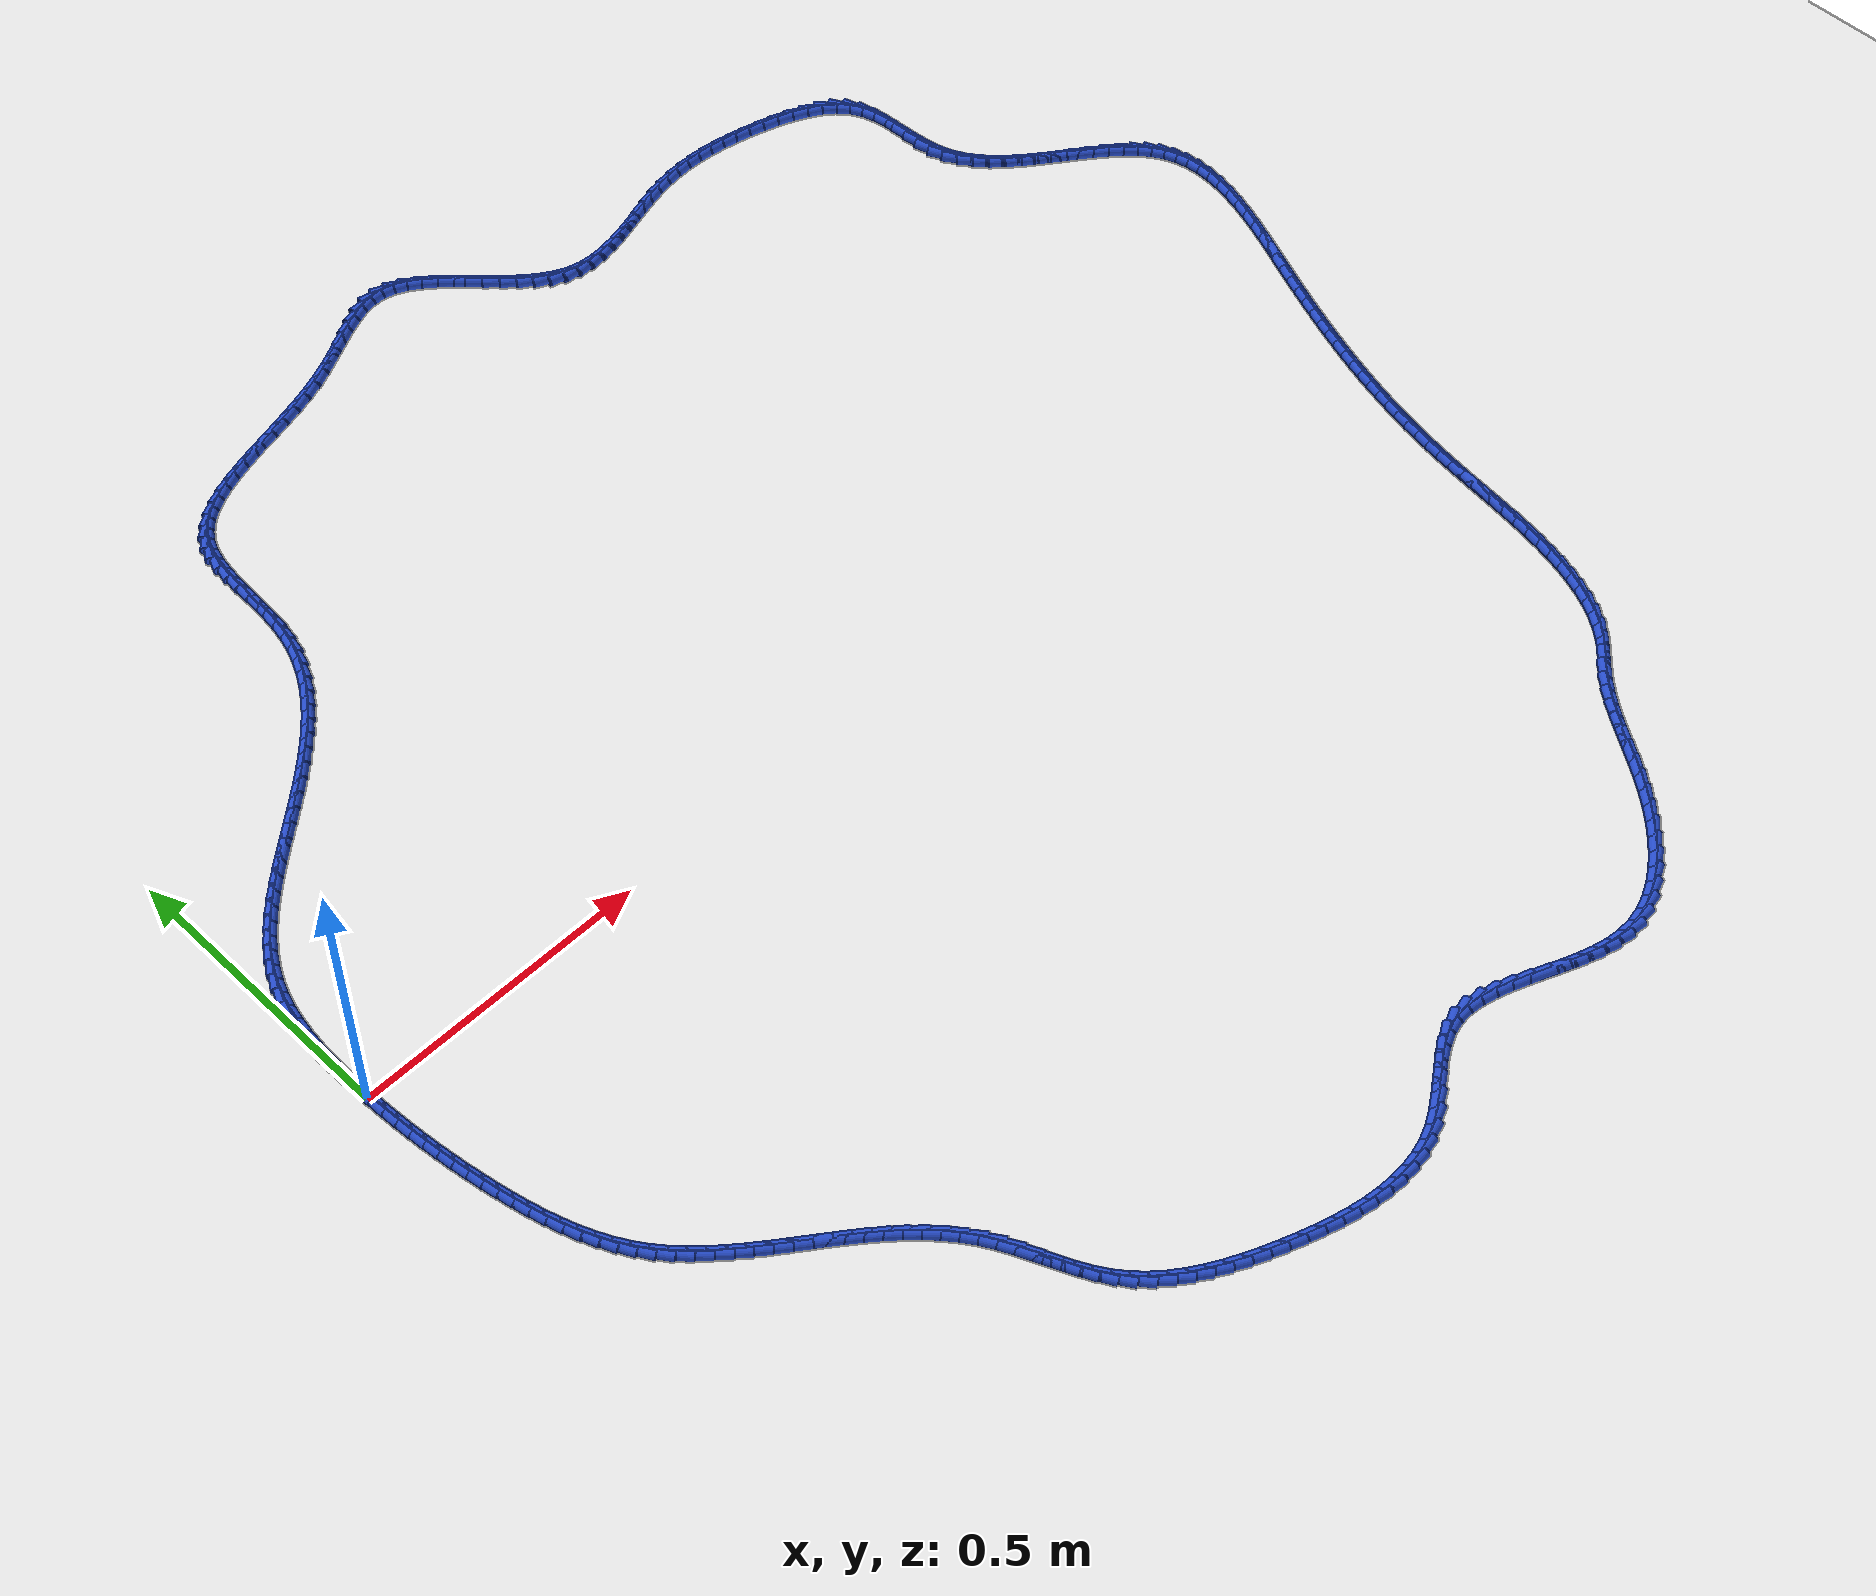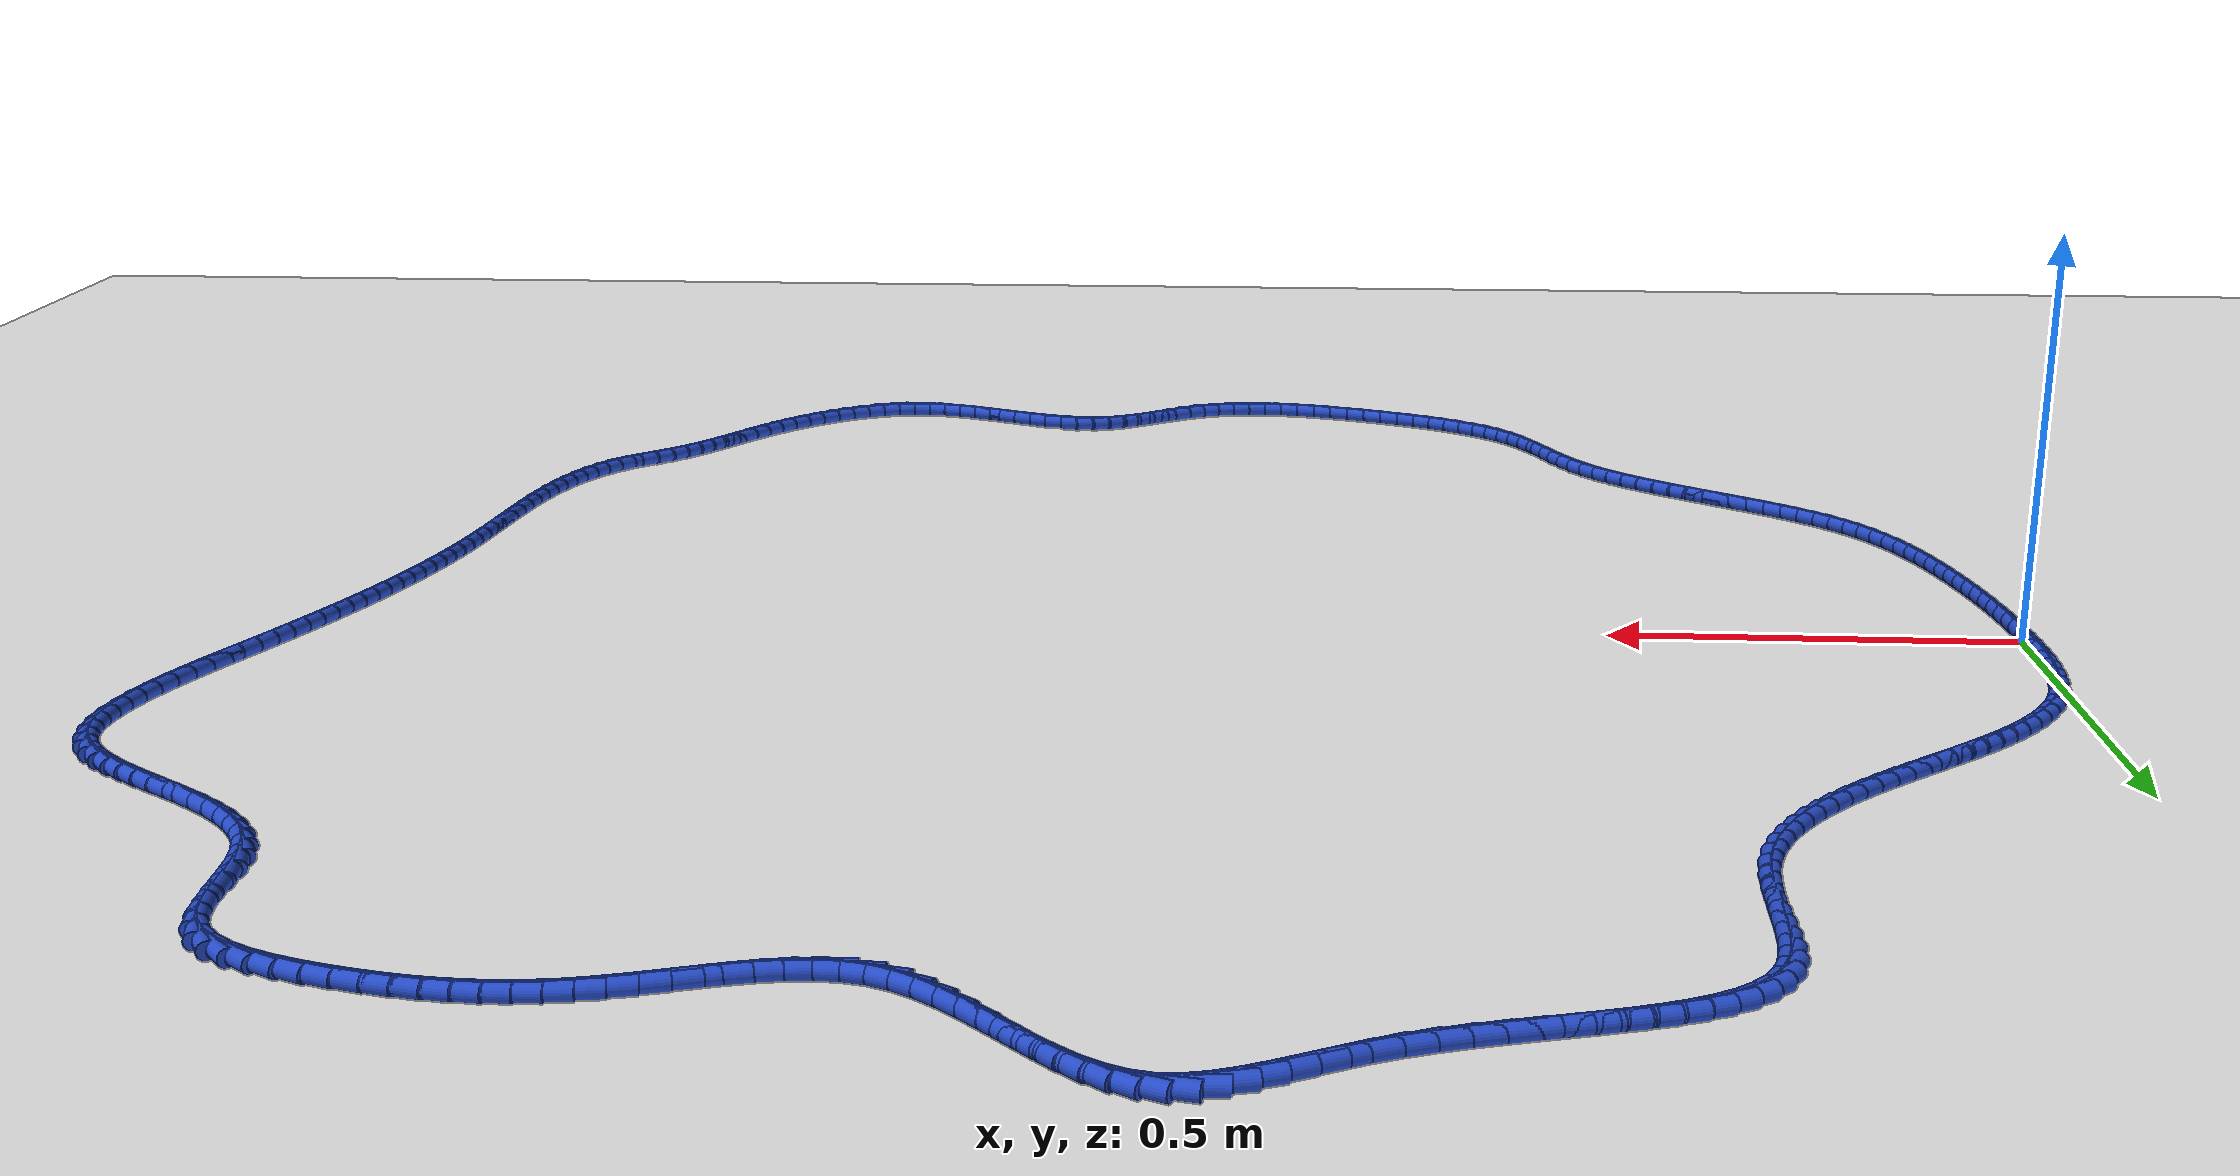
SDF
<sdf version="1.6">
 <world name="default">
  <light name="sun" type="directional">
   <pose>0 0 10 0 -0 0</pose>
   <diffuse>0.8 0.8 0.8 1</diffuse>
   <specular>0.2 0.2 0.2 1</specular>
   <attenuation>
    <range>1000</range>
    <constant>0.9</constant>
    <linear>0.01</linear>
    <quadratic>0.001</quadratic>
   </attenuation>
   <direction>-0.5 0.1 -0.9</direction>
  </light>
  <model name="ground_plane">
   <static>1</static>
   <link name="link">
    <collision name="collision">
     <geometry><plane><normal>0 0 1</normal><size>100 100</size></plane></geometry>
     <surface><friction><ode><mu>100</mu><mu2>50</mu2></ode></friction></surface>
    </collision>
    <visual name="visual">
     <cast_shadows>0</cast_shadows>
     <geometry><plane><normal>0 0 1</normal><size>100 100</size></plane></geometry>
     <material>
      <script><uri>file://media/materials/scripts/gazebo.material</uri><name>Gazebo/WhiteGlow</name></script>
     </material>
    </visual>
   </link>
  </model>
  <gravity>0 0 -9.8</gravity>
  <magnetic_field>6e-06 2.3e-05 -4.2e-05</magnetic_field>
  <atmosphere type="adiabatic"/>
  <physics name="default_physics" default="0" type="ode">
   <max_step_size>0.001</max_step_size>
   <real_time_factor>1</real_time_factor>
   <real_time_update_rate>1000</real_time_update_rate>
  </physics>
  <scene><ambient>0.4 0.4 0.4 1</ambient><background>0.7 0.7 0.7 1</background><shadows>1</shadows></scene>
  <spherical_coordinates>
   <surface_model>EARTH_WGS84</surface_model>
   <latitude_deg>0</latitude_deg>
   <longitude_deg>0</longitude_deg>
   <elevation>0</elevation>
   <heading_deg>0</heading_deg>
  </spherical_coordinates>
  <model name="line">
   <link name="link_0">
    <pose>1.5178830414797062e-18 -2.0816681711721685e-17 0.01 0 1.57 -1.5357499179945358</pose>
    <collision name="collision">
     <geometry><cylinder><radius>0.01</radius><length>0.08</length></cylinder></geometry>
    </collision>
    <visual name="visual">
     <material>
      <script><name>Gazebo/Blue</name><uri>file://media/materials/scripts/gazebo.material</uri></script>
     </material>
     <geometry><cylinder><radius>0.01</radius><length>0.08</length></cylinder></geometry>
    </visual>
   </link>
   <link name="link_1">
    <pose>-0.0009531655299289681 0.027186102327906716 0.01 0 1.57 -1.557637908118741</pose>
    <collision name="collision">
     <geometry><cylinder><radius>0.01</radius><length>0.08</length></cylinder></geometry>
    </collision>
    <visual name="visual">
     <material>
      <script><name>Gazebo/Blue</name><uri>file://media/materials/scripts/gazebo.material</uri></script>
     </material>
     <geometry><cylinder><radius>0.01</radius><length>0.08</length></cylinder></geometry>
    </visual>
   </link>
   <link name="link_2">
    <pose>-0.0013129631149767533 0.05452805184836838 0.01 0 1.57 1.5550119378873457</pose>
    <collision name="collision">
     <geometry><cylinder><radius>0.01</radius><length>0.08</length></cylinder></geometry>
    </collision>
    <visual name="visual">
     <material>
      <script><name>Gazebo/Blue</name><uri>file://media/materials/scripts/gazebo.material</uri></script>
     </material>
     <geometry><cylinder><radius>0.01</radius><length>0.08</length></cylinder></geometry>
    </visual>
   </link>
   <link name="link_3">
    <pose>-0.0008815274611693338 0.08185884212786379 0.01 0 1.57 1.5185273356382447</pose>
    <collision name="collision">
     <geometry><cylinder><radius>0.01</radius><length>0.08</length></cylinder></geometry>
    </collision>
    <visual name="visual">
     <material>
      <script><name>Gazebo/Blue</name><uri>file://media/materials/scripts/gazebo.material</uri></script>
     </material>
     <geometry><cylinder><radius>0.01</radius><length>0.08</length></cylinder></geometry>
    </visual>
   </link>
   <link name="link_4">
    <pose>0.0005390067254673054 0.10901146673287176 0.01 0 1.57 1.4738336928515299</pose>
    <collision name="collision">
     <geometry><cylinder><radius>0.01</radius><length>0.08</length></cylinder></geometry>
    </collision>
    <visual name="visual">
     <material>
      <script><name>Gazebo/Blue</name><uri>file://media/materials/scripts/gazebo.material</uri></script>
     </material>
     <geometry><cylinder><radius>0.01</radius><length>0.08</length></cylinder></geometry>
    </visual>
   </link>
   <link name="link_5">
    <pose>0.0031465047389071825 0.13581891922987116 0.01 0 1.57 1.420120264435745</pose>
    <collision name="collision">
     <geometry><cylinder><radius>0.01</radius><length>0.08</length></cylinder></geometry>
    </collision>
    <visual name="visual">
     <material>
      <script><name>Gazebo/Blue</name><uri>file://media/materials/scripts/gazebo.material</uri></script>
     </material>
     <geometry><cylinder><radius>0.01</radius><length>0.08</length></cylinder></geometry>
    </visual>
   </link>
   <link name="link_6">
    <pose>0.007138831873124321 0.16211419318534087 0.01 0 1.57 1.3565005701241915</pose>
    <collision name="collision">
     <geometry><cylinder><radius>0.01</radius><length>0.08</length></cylinder></geometry>
    </collision>
    <visual name="visual">
     <material>
      <script><name>Gazebo/Blue</name><uri>file://media/materials/scripts/gazebo.material</uri></script>
     </material>
     <geometry><cylinder><radius>0.01</radius><length>0.08</length></cylinder></geometry>
    </visual>
   </link>
   <link name="link_7">
    <pose>0.012713853422092731 0.18773028216575968 0.01 0 1.57 1.282134098570749</pose>
    <collision name="collision">
     <geometry><cylinder><radius>0.01</radius><length>0.08</length></cylinder></geometry>
    </collision>
    <visual name="visual">
     <material>
      <script><name>Gazebo/Blue</name><uri>file://media/materials/scripts/gazebo.material</uri></script>
     </material>
     <geometry><cylinder><radius>0.01</radius><length>0.08</length></cylinder></geometry>
    </visual>
   </link>
   <link name="link_8">
    <pose>0.020069434679786426 0.21250017973760646 0.01 0 1.57 1.196468657600396</pose>
    <collision name="collision">
     <geometry><cylinder><radius>0.01</radius><length>0.08</length></cylinder></geometry>
    </collision>
    <visual name="visual">
     <material>
      <script><name>Gazebo/Blue</name><uri>file://media/materials/scripts/gazebo.material</uri></script>
     </material>
     <geometry><cylinder><radius>0.01</radius><length>0.08</length></cylinder></geometry>
    </visual>
   </link>
   <link name="link_9">
    <pose>0.02940251967727458 0.23625753849296213 0.01 0 1.57 1.1052526241479554</pose>
    <collision name="collision">
     <geometry><cylinder><radius>0.01</radius><length>0.08</length></cylinder></geometry>
    </collision>
    <visual name="visual">
     <material>
      <script><name>Gazebo/Blue</name><uri>file://media/materials/scripts/gazebo.material</uri></script>
     </material>
     <geometry><cylinder><radius>0.01</radius><length>0.08</length></cylinder></geometry>
    </visual>
   </link>
   <link name="link_10">
    <pose>0.04078887000763694 0.25892269890500574 0.01 0 1.57 1.0210862639564562</pose>
    <collision name="collision">
     <geometry><cylinder><radius>0.01</radius><length>0.08</length></cylinder></geometry>
    </collision>
    <visual name="visual">
     <material>
      <script><name>Gazebo/Blue</name><uri>file://media/materials/scripts/gazebo.material</uri></script>
     </material>
     <geometry><cylinder><radius>0.01</radius><length>0.08</length></cylinder></geometry>
    </visual>
   </link>
   <link name="link_11">
    <pose>0.0540634809570943 0.28058823367237556 0.01 0 1.57 0.9464981407887155</pose>
    <collision name="collision">
     <geometry><cylinder><radius>0.01</radius><length>0.08</length></cylinder></geometry>
    </collision>
    <visual name="visual">
     <material>
      <script><name>Gazebo/Blue</name><uri>file://media/materials/scripts/gazebo.material</uri></script>
     </material>
     <geometry><cylinder><radius>0.01</radius><length>0.08</length></cylinder></geometry>
    </visual>
   </link>
   <link name="link_12">
    <pose>0.0690329147169243 0.3013670551138274 0.01 0 1.57 0.8819882340618641</pose>
    <collision name="collision">
     <geometry><cylinder><radius>0.01</radius><length>0.08</length></cylinder></geometry>
    </collision>
    <visual name="visual">
     <material>
      <script><name>Gazebo/Blue</name><uri>file://media/materials/scripts/gazebo.material</uri></script>
     </material>
     <geometry><cylinder><radius>0.01</radius><length>0.08</length></cylinder></geometry>
    </visual>
   </link>
   <link name="link_13">
    <pose>0.08550373347840472 0.3213720755481173 0.01 0 1.57 0.8275403209935247</pose>
    <collision name="collision">
     <geometry><cylinder><radius>0.01</radius><length>0.08</length></cylinder></geometry>
    </collision>
    <visual name="visual">
     <material>
      <script><name>Gazebo/Blue</name><uri>file://media/materials/scripts/gazebo.material</uri></script>
     </material>
     <geometry><cylinder><radius>0.01</radius><length>0.08</length></cylinder></geometry>
    </visual>
   </link>
   <link name="link_14">
    <pose>0.10328249943281334 0.3407162072940013 0.01 0 1.57 0.782821320352184</pose>
    <collision name="collision">
     <geometry><cylinder><radius>0.01</radius><length>0.08</length></cylinder></geometry>
    </collision>
    <visual name="visual">
     <material>
      <script><name>Gazebo/Blue</name><uri>file://media/materials/scripts/gazebo.material</uri></script>
     </material>
     <geometry><cylinder><radius>0.01</radius><length>0.08</length></cylinder></geometry>
    </visual>
   </link>
   <link name="link_15">
    <pose>0.12217577477142778 0.3595123626702354 0.01 0 1.57 0.7473487194045153</pose>
    <collision name="collision">
     <geometry><cylinder><radius>0.01</radius><length>0.08</length></cylinder></geometry>
    </collision>
    <visual name="visual">
     <material>
      <script><name>Gazebo/Blue</name><uri>file://media/materials/scripts/gazebo.material</uri></script>
     </material>
     <geometry><cylinder><radius>0.01</radius><length>0.08</length></cylinder></geometry>
    </visual>
   </link>
   <link name="link_16">
    <pose>0.14199012168552588 0.3778734539955757 0.01 0 1.57 0.7206112674440949</pose>
    <collision name="collision">
     <geometry><cylinder><radius>0.01</radius><length>0.08</length></cylinder></geometry>
    </collision>
    <visual name="visual">
     <material>
      <script><name>Gazebo/Blue</name><uri>file://media/materials/scripts/gazebo.material</uri></script>
     </material>
     <geometry><cylinder><radius>0.01</radius><length>0.08</length></cylinder></geometry>
    </visual>
   </link>
   <link name="link_17">
    <pose>0.16253210236638538 0.3959123935887782 0.01 0 1.57 0.702146659618832</pose>
    <collision name="collision">
     <geometry><cylinder><radius>0.01</radius><length>0.08</length></cylinder></geometry>
    </collision>
    <visual name="visual">
     <material>
      <script><name>Gazebo/Blue</name><uri>file://media/materials/scripts/gazebo.material</uri></script>
     </material>
     <geometry><cylinder><radius>0.01</radius><length>0.08</length></cylinder></geometry>
    </visual>
   </link>
   <link name="link_18">
    <pose>0.18360827900528395 0.413742093768599 0.01 0 1.57 0.691586653170084</pose>
    <collision name="collision">
     <geometry><cylinder><radius>0.01</radius><length>0.08</length></cylinder></geometry>
    </collision>
    <visual name="visual">
     <material>
      <script><name>Gazebo/Blue</name><uri>file://media/materials/scripts/gazebo.material</uri></script>
     </material>
     <geometry><cylinder><radius>0.01</radius><length>0.08</length></cylinder></geometry>
    </visual>
   </link>
   <link name="link_19">
    <pose>0.20502521379349942 0.4314754668537938 0.01 0 1.57 0.6886800660613575</pose>
    <collision name="collision">
     <geometry><cylinder><radius>0.01</radius><length>0.08</length></cylinder></geometry>
    </collision>
    <visual name="visual">
     <material>
      <script><name>Gazebo/Blue</name><uri>file://media/materials/scripts/gazebo.material</uri></script>
     </material>
     <geometry><cylinder><radius>0.01</radius><length>0.08</length></cylinder></geometry>
    </visual>
   </link>
   <link name="link_20">
    <pose>0.22658946892230936 0.44922542516311886 0.01 0 1.57 0.6933014606268385</pose>
    <collision name="collision">
     <geometry><cylinder><radius>0.01</radius><length>0.08</length></cylinder></geometry>
    </collision>
    <visual name="visual">
     <material>
      <script><name>Gazebo/Blue</name><uri>file://media/materials/scripts/gazebo.material</uri></script>
     </material>
     <geometry><cylinder><radius>0.01</radius><length>0.08</length></cylinder></geometry>
    </visual>
   </link>
   <link name="link_21">
    <pose>0.24810760658299172 0.4671048810153302 0.01 0 1.57 0.7054326351661455</pose>
    <collision name="collision">
     <geometry><cylinder><radius>0.01</radius><length>0.08</length></cylinder></geometry>
    </collision>
    <visual name="visual">
     <material>
      <script><name>Gazebo/Blue</name><uri>file://media/materials/scripts/gazebo.material</uri></script>
     </material>
     <geometry><cylinder><radius>0.01</radius><length>0.08</length></cylinder></geometry>
    </visual>
   </link>
   <link name="link_22">
    <pose>0.26938643429832254 0.48522631328447346 0.01 0 1.57 0.7245437272667095</pose>
    <collision name="collision">
     <geometry><cylinder><radius>0.01</radius><length>0.08</length></cylinder></geometry>
    </collision>
    <visual name="visual">
     <material>
      <script><name>Gazebo/Blue</name><uri>file://media/materials/scripts/gazebo.material</uri></script>
     </material>
     <geometry><cylinder><radius>0.01</radius><length>0.08</length></cylinder></geometry>
    </visual>
   </link>
   <link name="link_23">
    <pose>0.29024180587092224 0.5036862181347899 0.01 0 1.57 0.750030642472186</pose>
    <collision name="collision">
     <geometry><cylinder><radius>0.01</radius><length>0.08</length></cylinder></geometry>
    </collision>
    <visual name="visual">
     <material>
      <script><name>Gazebo/Blue</name><uri>file://media/materials/scripts/gazebo.material</uri></script>
     </material>
     <geometry><cylinder><radius>0.01</radius><length>0.08</length></cylinder></geometry>
    </visual>
   </link>
   <link name="link_24">
    <pose>0.310501050136239 0.5225608179690585 0.01 0 1.57 0.7821302844321567</pose>
    <collision name="collision">
     <geometry><cylinder><radius>0.01</radius><length>0.08</length></cylinder></geometry>
    </collision>
    <visual name="visual">
     <material>
      <script><name>Gazebo/Blue</name><uri>file://media/materials/scripts/gazebo.material</uri></script>
     </material>
     <geometry><cylinder><radius>0.01</radius><length>0.08</length></cylinder></geometry>
    </visual>
   </link>
   <link name="link_25">
    <pose>0.3299922356403125 0.5419250282904349 0.01 0 1.57 0.8211818290204305</pose>
    <collision name="collision">
     <geometry><cylinder><radius>0.01</radius><length>0.08</length></cylinder></geometry>
    </collision>
    <visual name="visual">
     <material>
      <script><name>Gazebo/Blue</name><uri>file://media/materials/scripts/gazebo.material</uri></script>
     </material>
     <geometry><cylinder><radius>0.01</radius><length>0.08</length></cylinder></geometry>
    </visual>
   </link>
   <link name="link_26">
    <pose>0.34854343092918194 0.5618537646020741 0.01 0 1.57 0.8675363842457605</pose>
    <collision name="collision">
     <geometry><cylinder><radius>0.01</radius><length>0.08</length></cylinder></geometry>
    </collision>
    <visual name="visual">
     <material>
      <script><name>Gazebo/Blue</name><uri>file://media/materials/scripts/gazebo.material</uri></script>
     </material>
     <geometry><cylinder><radius>0.01</radius><length>0.08</length></cylinder></geometry>
    </visual>
   </link>
   <link name="link_27">
    <pose>0.36598270454888726 0.5824219424071317 0.01 0 1.57 0.9215011328684851</pose>
    <collision name="collision">
     <geometry><cylinder><radius>0.01</radius><length>0.08</length></cylinder></geometry>
    </collision>
    <visual name="visual">
     <material>
      <script><name>Gazebo/Blue</name><uri>file://media/materials/scripts/gazebo.material</uri></script>
     </material>
     <geometry><cylinder><radius>0.01</radius><length>0.08</length></cylinder></geometry>
    </visual>
   </link>
   <link name="link_28">
    <pose>0.38213812504546796 0.6037044772087633 0.01 0 1.57 0.9832612961613444</pose>
    <collision name="collision">
     <geometry><cylinder><radius>0.01</radius><length>0.08</length></cylinder></geometry>
    </collision>
    <visual name="visual">
     <material>
      <script><name>Gazebo/Blue</name><uri>file://media/materials/scripts/gazebo.material</uri></script>
     </material>
     <geometry><cylinder><radius>0.01</radius><length>0.08</length></cylinder></geometry>
    </visual>
   </link>
   <link name="link_29">
    <pose>0.3968377609649634 0.6257762845101236 0.01 0 1.57 1.0527803680394514</pose>
    <collision name="collision">
     <geometry><cylinder><radius>0.01</radius><length>0.08</length></cylinder></geometry>
    </collision>
    <visual name="visual">
     <material>
      <script><name>Gazebo/Blue</name><uri>file://media/materials/scripts/gazebo.material</uri></script>
     </material>
     <geometry><cylinder><radius>0.01</radius><length>0.08</length></cylinder></geometry>
    </visual>
   </link>
   <link name="link_30">
    <pose>0.40990968085341356 0.6487122798143686 0.01 0 1.57 1.129688077431138</pose>
    <collision name="collision">
     <geometry><cylinder><radius>0.01</radius><length>0.08</length></cylinder></geometry>
    </collision>
    <visual name="visual">
     <material>
      <script><name>Gazebo/Blue</name><uri>file://media/materials/scripts/gazebo.material</uri></script>
     </material>
     <geometry><cylinder><radius>0.01</radius><length>0.08</length></cylinder></geometry>
    </visual>
   </link>
   <link name="link_31">
    <pose>0.4211819532568576 0.6725873786246532 0.01 0 1.57 1.213178908952952</pose>
    <collision name="collision">
     <geometry><cylinder><radius>0.01</radius><length>0.08</length></cylinder></geometry>
    </collision>
    <visual name="visual">
     <material>
      <script><name>Gazebo/Blue</name><uri>file://media/materials/scripts/gazebo.material</uri></script>
     </material>
     <geometry><cylinder><radius>0.01</radius><length>0.08</length></cylinder></geometry>
    </visual>
   </link>
   <link name="link_32">
    <pose>0.43048264672133546 0.6974764964441335 0.01 0 1.57 1.3019571126695757</pose>
    <collision name="collision">
     <geometry><cylinder><radius>0.01</radius><length>0.08</length></cylinder></geometry>
    </collision>
    <visual name="visual">
     <material>
      <script><name>Gazebo/Blue</name><uri>file://media/materials/scripts/gazebo.material</uri></script>
     </material>
     <geometry><cylinder><radius>0.01</radius><length>0.08</length></cylinder></geometry>
    </visual>
   </link>
   <link name="link_33">
    <pose>0.43763982979288635 0.7234545487759642 0.01 0 1.57 1.3914254881474022</pose>
    <collision name="collision">
     <geometry><cylinder><radius>0.01</radius><length>0.08</length></cylinder></geometry>
    </collision>
    <visual name="visual">
     <material>
      <script><name>Gazebo/Blue</name><uri>file://media/materials/scripts/gazebo.material</uri></script>
     </material>
     <geometry><cylinder><radius>0.01</radius><length>0.08</length></cylinder></geometry>
    </visual>
   </link>
   <link name="link_34">
    <pose>0.4425530055776064 0.7505513190667006 0.01 0 1.57 1.4603277855345242</pose>
    <collision name="collision">
     <geometry><cylinder><radius>0.01</radius><length>0.08</length></cylinder></geometry>
    </collision>
    <visual name="visual">
     <material>
      <script><name>Gazebo/Blue</name><uri>file://media/materials/scripts/gazebo.material</uri></script>
     </material>
     <geometry><cylinder><radius>0.01</radius><length>0.08</length></cylinder></geometry>
    </visual>
   </link>
   <link name="link_35">
    <pose>0.44564901861669476 0.7784634186473538 0.01 0 1.57 1.502227634199551</pose>
    <collision name="collision">
     <geometry><cylinder><radius>0.01</radius><length>0.08</length></cylinder></geometry>
    </collision>
    <visual name="visual">
     <material>
      <script><name>Gazebo/Blue</name><uri>file://media/materials/scripts/gazebo.material</uri></script>
     </material>
     <geometry><cylinder><radius>0.01</radius><length>0.08</length></cylinder></geometry>
    </visual>
   </link>
   <link name="link_36">
    <pose>0.44759083306457664 0.8067382794637729 0.01 0 1.57 1.5193349013094481</pose>
    <collision name="collision">
     <geometry><cylinder><radius>0.01</radius><length>0.08</length></cylinder></geometry>
    </collision>
    <visual name="visual">
     <material>
      <script><name>Gazebo/Blue</name><uri>file://media/materials/scripts/gazebo.material</uri></script>
     </material>
     <geometry><cylinder><radius>0.01</radius><length>0.08</length></cylinder></geometry>
    </visual>
   </link>
   <link name="link_37">
    <pose>0.4490425217911388 0.8349226329800091 0.01 0 1.57 1.5120506157369022</pose>
    <collision name="collision">
     <geometry><cylinder><radius>0.01</radius><length>0.08</length></cylinder></geometry>
    </collision>
    <visual name="visual">
     <material>
      <script><name>Gazebo/Blue</name><uri>file://media/materials/scripts/gazebo.material</uri></script>
     </material>
     <geometry><cylinder><radius>0.01</radius><length>0.08</length></cylinder></geometry>
    </visual>
   </link>
   <link name="link_38">
    <pose>0.450668157666268 0.8625632106601149 0.01 0 1.57 1.4785912096408516</pose>
    <collision name="collision">
     <geometry><cylinder><radius>0.01</radius><length>0.08</length></cylinder></geometry>
    </collision>
    <visual name="visual">
     <material>
      <script><name>Gazebo/Blue</name><uri>file://media/materials/scripts/gazebo.material</uri></script>
     </material>
     <geometry><cylinder><radius>0.01</radius><length>0.08</length></cylinder></geometry>
    </visual>
   </link>
   <link name="link_39">
    <pose>0.4531318135598506 0.8892067439681415 0.01 0 1.57 1.414664179030179</pose>
    <collision name="collision">
     <geometry><cylinder><radius>0.01</radius><length>0.08</length></cylinder></geometry>
    </collision>
    <visual name="visual">
     <material>
      <script><name>Gazebo/Blue</name><uri>file://media/materials/scripts/gazebo.material</uri></script>
     </material>
     <geometry><cylinder><radius>0.01</radius><length>0.08</length></cylinder></geometry>
    </visual>
   </link>
   <link name="link_40">
    <pose>0.45709756234177396 0.9143999643681415 0.01 0 1.57 1.3133496488750067</pose>
    <collision name="collision">
     <geometry><cylinder><radius>0.01</radius><length>0.08</length></cylinder></geometry>
    </collision>
    <visual name="visual">
     <material>
      <script><name>Gazebo/Blue</name><uri>file://media/materials/scripts/gazebo.material</uri></script>
     </material>
     <geometry><cylinder><radius>0.01</radius><length>0.08</length></cylinder></geometry>
    </visual>
   </link>
   <link name="link_41">
    <pose>0.46322947688192406 0.937689603324166 0.01 0 1.57 1.1663318433616883</pose>
    <collision name="collision">
     <geometry><cylinder><radius>0.01</radius><length>0.08</length></cylinder></geometry>
    </collision>
    <visual name="visual">
     <material>
      <script><name>Gazebo/Blue</name><uri>file://media/materials/scripts/gazebo.material</uri></script>
     </material>
     <geometry><cylinder><radius>0.01</radius><length>0.08</length></cylinder></geometry>
    </visual>
   </link>
   <link name="link_42">
    <pose>0.4721904749100256 0.9586232995167805 0.01 0 1.57 0.9841497294428114</pose>
    <collision name="collision">
     <geometry><cylinder><radius>0.01</radius><length>0.08</length></cylinder></geometry>
    </collision>
    <visual name="visual">
     <material>
      <script><name>Gazebo/Blue</name><uri>file://media/materials/scripts/gazebo.material</uri></script>
     </material>
     <geometry><cylinder><radius>0.01</radius><length>0.08</length></cylinder></geometry>
    </visual>
   </link>
   <link name="link_43">
    <pose>0.48437746749637645 0.976957606216957 0.01 0 1.57 0.8097848974648232</pose>
    <collision name="collision">
     <geometry><cylinder><radius>0.01</radius><length>0.08</length></cylinder></geometry>
    </collision>
    <visual name="visual">
     <material>
      <script><name>Gazebo/Blue</name><uri>file://media/materials/scripts/gazebo.material</uri></script>
     </material>
     <geometry><cylinder><radius>0.01</radius><length>0.08</length></cylinder></geometry>
    </visual>
   </link>
   <link name="link_44">
    <pose>0.4995831481050269 0.9929236132129062 0.01 0 1.57 0.6591628789713916</pose>
    <collision name="collision">
     <geometry><cylinder><radius>0.01</radius><length>0.08</length></cylinder></geometry>
    </collision>
    <visual name="visual">
     <material>
      <script><name>Gazebo/Blue</name><uri>file://media/materials/scripts/gazebo.material</uri></script>
     </material>
     <geometry><cylinder><radius>0.01</radius><length>0.08</length></cylinder></geometry>
    </visual>
   </link>
   <link name="link_45">
    <pose>0.5175167677088187 1.0068179438171176 0.01 0 1.57 0.5366858220154567</pose>
    <collision name="collision">
     <geometry><cylinder><radius>0.01</radius><length>0.08</length></cylinder></geometry>
    </collision>
    <visual name="visual">
     <material>
      <script><name>Gazebo/Blue</name><uri>file://media/materials/scripts/gazebo.material</uri></script>
     </material>
     <geometry><cylinder><radius>0.01</radius><length>0.08</length></cylinder></geometry>
    </visual>
   </link>
   <link name="link_46">
    <pose>0.5378875772805929 1.0189372213420802 0.01 0 1.57 0.44145911355571316</pose>
    <collision name="collision">
     <geometry><cylinder><radius>0.01</radius><length>0.08</length></cylinder></geometry>
    </collision>
    <visual name="visual">
     <material>
      <script><name>Gazebo/Blue</name><uri>file://media/materials/scripts/gazebo.material</uri></script>
     </material>
     <geometry><cylinder><radius>0.01</radius><length>0.08</length></cylinder></geometry>
    </visual>
   </link>
   <link name="link_47">
    <pose>0.560404827793191 1.029578069100282 0.01 0 1.57 0.3702023694781553</pose>
    <collision name="collision">
     <geometry><cylinder><radius>0.01</radius><length>0.08</length></cylinder></geometry>
    </collision>
    <visual name="visual">
     <material>
      <script><name>Gazebo/Blue</name><uri>file://media/materials/scripts/gazebo.material</uri></script>
     </material>
     <geometry><cylinder><radius>0.01</radius><length>0.08</length></cylinder></geometry>
    </visual>
   </link>
   <link name="link_48">
    <pose>0.5847777702194545 1.039037110404213 0.01 0 1.57 0.3192466002488659</pose>
    <collision name="collision">
     <geometry><cylinder><radius>0.01</radius><length>0.08</length></cylinder></geometry>
    </collision>
    <visual name="visual">
     <material>
      <script><name>Gazebo/Blue</name><uri>file://media/materials/scripts/gazebo.material</uri></script>
     </material>
     <geometry><cylinder><radius>0.01</radius><length>0.08</length></cylinder></geometry>
    </visual>
   </link>
   <link name="link_49">
    <pose>0.6107156555322247 1.0476109685663624 0.01 0 1.57 0.285433920319902</pose>
    <collision name="collision">
     <geometry><cylinder><radius>0.01</radius><length>0.08</length></cylinder></geometry>
    </collision>
    <visual name="visual">
     <material>
      <script><name>Gazebo/Blue</name><uri>file://media/materials/scripts/gazebo.material</uri></script>
     </material>
     <geometry><cylinder><radius>0.01</radius><length>0.08</length></cylinder></geometry>
    </visual>
   </link>
   <link name="link_50">
    <pose>0.6379277347043428 1.0555962668992183 0.01 0 1.57 0.26637331032321054</pose>
    <collision name="collision">
     <geometry><cylinder><radius>0.01</radius><length>0.08</length></cylinder></geometry>
    </collision>
    <visual name="visual">
     <material>
      <script><name>Gazebo/Blue</name><uri>file://media/materials/scripts/gazebo.material</uri></script>
     </material>
     <geometry><cylinder><radius>0.01</radius><length>0.08</length></cylinder></geometry>
    </visual>
   </link>
   <link name="link_51">
    <pose>0.6661232587086502 1.0632896287152702 0.01 0 1.57 0.26042538826020223</pose>
    <collision name="collision">
     <geometry><cylinder><radius>0.01</radius><length>0.08</length></cylinder></geometry>
    </collision>
    <visual name="visual">
     <material>
      <script><name>Gazebo/Blue</name><uri>file://media/materials/scripts/gazebo.material</uri></script>
     </material>
     <geometry><cylinder><radius>0.01</radius><length>0.08</length></cylinder></geometry>
    </visual>
   </link>
   <link name="link_52">
    <pose>0.6950114785179885 1.0709876773270068 0.01 0 1.57 0.266605745631477</pose>
    <collision name="collision">
     <geometry><cylinder><radius>0.01</radius><length>0.08</length></cylinder></geometry>
    </collision>
    <visual name="visual">
     <material>
      <script><name>Gazebo/Blue</name><uri>file://media/materials/scripts/gazebo.material</uri></script>
     </material>
     <geometry><cylinder><radius>0.01</radius><length>0.08</length></cylinder></geometry>
    </visual>
   </link>
   <link name="link_53">
    <pose>0.7243016451051989 1.0789870360469176 0.01 0 1.57 0.28448025632831053</pose>
    <collision name="collision">
     <geometry><cylinder><radius>0.01</radius><length>0.08</length></cylinder></geometry>
    </collision>
    <visual name="visual">
     <material>
      <script><name>Gazebo/Blue</name><uri>file://media/materials/scripts/gazebo.material</uri></script>
     </material>
     <geometry><cylinder><radius>0.01</radius><length>0.08</length></cylinder></geometry>
    </visual>
   </link>
   <link name="link_54">
    <pose>0.7537030094431226 1.0875843281874908 0.01 0 1.57 0.31406969195523887</pose>
    <collision name="collision">
     <geometry><cylinder><radius>0.01</radius><length>0.08</length></cylinder></geometry>
    </collision>
    <visual name="visual">
     <material>
      <script><name>Gazebo/Blue</name><uri>file://media/materials/scripts/gazebo.material</uri></script>
     </material>
     <geometry><cylinder><radius>0.01</radius><length>0.08</length></cylinder></geometry>
    </visual>
   </link>
   <link name="link_55">
    <pose>0.7829248225046013 1.097076177061216 0.01 0 1.57 0.35575494510192446</pose>
    <collision name="collision">
     <geometry><cylinder><radius>0.01</radius><length>0.08</length></cylinder></geometry>
    </collision>
    <visual name="visual">
     <material>
      <script><name>Gazebo/Blue</name><uri>file://media/materials/scripts/gazebo.material</uri></script>
     </material>
     <geometry><cylinder><radius>0.01</radius><length>0.08</length></cylinder></geometry>
    </visual>
   </link>
   <link name="link_56">
    <pose>0.8116763352624761 1.107759205980582 0.01 0 1.57 0.40938998920742864</pose>
    <collision name="collision">
     <geometry><cylinder><radius>0.01</radius><length>0.08</length></cylinder></geometry>
    </collision>
    <visual name="visual">
     <material>
      <script><name>Gazebo/Blue</name><uri>file://media/materials/scripts/gazebo.material</uri></script>
     </material>
     <geometry><cylinder><radius>0.01</radius><length>0.08</length></cylinder></geometry>
    </visual>
   </link>
   <link name="link_57">
    <pose>0.8396728514470233 1.1199070665959758 0.01 0 1.57 0.4562645309256227</pose>
    <collision name="collision">
     <geometry><cylinder><radius>0.01</radius><length>0.08</length></cylinder></geometry>
    </collision>
    <visual name="visual">
     <material>
      <script><name>Gazebo/Blue</name><uri>file://media/materials/scripts/gazebo.material</uri></script>
     </material>
     <geometry><cylinder><radius>0.01</radius><length>0.08</length></cylinder></geometry>
    </visual>
   </link>
   <link name="link_58">
    <pose>0.8667826835239762 1.133212705811675 0.01 0 1.57 0.47632569828253873</pose>
    <collision name="collision">
     <geometry><cylinder><radius>0.01</radius><length>0.08</length></cylinder></geometry>
    </collision>
    <visual name="visual">
     <material>
      <script><name>Gazebo/Blue</name><uri>file://media/materials/scripts/gazebo.material</uri></script>
     </material>
     <geometry><cylinder><radius>0.01</radius><length>0.08</length></cylinder></geometry>
    </visual>
   </link>
   <link name="link_59">
    <pose>0.8930352333797654 1.1467576976527027 0.01 0 1.57 0.4674352019873801</pose>
    <collision name="collision">
     <geometry><cylinder><radius>0.01</radius><length>0.08</length></cylinder></geometry>
    </collision>
    <visual name="visual">
     <material>
      <script><name>Gazebo/Blue</name><uri>file://media/materials/scripts/gazebo.material</uri></script>
     </material>
     <geometry><cylinder><radius>0.01</radius><length>0.08</length></cylinder></geometry>
    </visual>
   </link>
   <link name="link_60">
    <pose>0.9184675731372824 1.1595945057622288 0.01 0 1.57 0.4258507213149521</pose>
    <collision name="collision">
     <geometry><cylinder><radius>0.01</radius><length>0.08</length></cylinder></geometry>
    </collision>
    <visual name="visual">
     <material>
      <script><name>Gazebo/Blue</name><uri>file://media/materials/scripts/gazebo.material</uri></script>
     </material>
     <geometry><cylinder><radius>0.01</radius><length>0.08</length></cylinder></geometry>
    </visual>
   </link>
   <link name="link_61">
    <pose>0.9431167749194173 1.1707755937834228 0.01 0 1.57 0.34454423634567055</pose>
    <collision name="collision">
     <geometry><cylinder><radius>0.01</radius><length>0.08</length></cylinder></geometry>
    </collision>
    <visual name="visual">
     <material>
      <script><name>Gazebo/Blue</name><uri>file://media/materials/scripts/gazebo.material</uri></script>
     </material>
     <geometry><cylinder><radius>0.01</radius><length>0.08</length></cylinder></geometry>
    </visual>
   </link>
   <link name="link_62">
    <pose>0.9670199108490608 1.179353425359454 0.01 0 1.57 0.21343623160899192</pose>
    <collision name="collision">
     <geometry><cylinder><radius>0.01</radius><length>0.08</length></cylinder></geometry>
    </collision>
    <visual name="visual">
     <material>
      <script><name>Gazebo/Blue</name><uri>file://media/materials/scripts/gazebo.material</uri></script>
     </material>
     <geometry><cylinder><radius>0.01</radius><length>0.08</length></cylinder></geometry>
    </visual>
   </link>
   <link name="link_63">
    <pose>0.9902140530491045 1.1843804641334919 0.01 0 1.57 0.023470710860181494</pose>
    <collision name="collision">
     <geometry><cylinder><radius>0.01</radius><length>0.08</length></cylinder></geometry>
    </collision>
    <visual name="visual">
     <material>
      <script><name>Gazebo/Blue</name><uri>file://media/materials/scripts/gazebo.material</uri></script>
     </material>
     <geometry><cylinder><radius>0.01</radius><length>0.08</length></cylinder></geometry>
    </visual>
   </link>
   <link name="link_64">
    <pose>1.012736273642439 1.184909173748707 0.01 0 1.57 -0.21345648533254488</pose>
    <collision name="collision">
     <geometry><cylinder><radius>0.01</radius><length>0.08</length></cylinder></geometry>
    </collision>
    <visual name="visual">
     <material>
      <script><name>Gazebo/Blue</name><uri>file://media/materials/scripts/gazebo.material</uri></script>
     </material>
     <geometry><cylinder><radius>0.01</radius><length>0.08</length></cylinder></geometry>
    </visual>
   </link>
   <link name="link_65">
    <pose>1.034632316392361 1.1801630174027262 0.01 0 1.57 -0.4232969018457366</pose>
    <collision name="collision">
     <geometry><cylinder><radius>0.01</radius><length>0.08</length></cylinder></geometry>
    </collision>
    <visual name="visual">
     <material>
      <script><name>Gazebo/Blue</name><uri>file://media/materials/scripts/gazebo.material</uri></script>
     </material>
     <geometry><cylinder><radius>0.01</radius><length>0.08</length></cylinder></geometry>
    </visual>
   </link>
   <link name="link_66">
    <pose>1.056007130937334 1.1705329626868761 0.01 0 1.57 -0.5762417381620799</pose>
    <collision name="collision">
     <geometry><cylinder><radius>0.01</radius><length>0.08</length></cylinder></geometry>
    </collision>
    <visual name="visual">
     <material>
      <script><name>Gazebo/Blue</name><uri>file://media/materials/scripts/gazebo.material</uri></script>
     </material>
     <geometry><cylinder><radius>0.01</radius><length>0.08</length></cylinder></geometry>
    </visual>
   </link>
   <link name="link_67">
    <pose>1.0769904060351025 1.1568978178058498 0.01 0 1.57 -0.680090681509359</pose>
    <collision name="collision">
     <geometry><cylinder><radius>0.01</radius><length>0.08</length></cylinder></geometry>
    </collision>
    <visual name="visual">
     <material>
      <script><name>Gazebo/Blue</name><uri>file://media/materials/scripts/gazebo.material</uri></script>
     </material>
     <geometry><cylinder><radius>0.01</radius><length>0.08</length></cylinder></geometry>
    </visual>
   </link>
   <link name="link_68">
    <pose>1.0977119134137796 1.1401380270903283 0.01 0 1.57 -0.7453746159096243</pose>
    <collision name="collision">
     <geometry><cylinder><radius>0.01</radius><length>0.08</length></cylinder></geometry>
    </collision>
    <visual name="visual">
     <material>
      <script><name>Gazebo/Blue</name><uri>file://media/materials/scripts/gazebo.material</uri></script>
     </material>
     <geometry><cylinder><radius>0.01</radius><length>0.08</length></cylinder></geometry>
    </visual>
   </link>
   <link name="link_69">
    <pose>1.1183014248014795 1.1211340348709946 0.01 0 1.57 -0.7800377572470345</pose>
    <collision name="collision">
     <geometry><cylinder><radius>0.01</radius><length>0.08</length></cylinder></geometry>
    </collision>
    <visual name="visual">
     <material>
      <script><name>Gazebo/Blue</name><uri>file://media/materials/scripts/gazebo.material</uri></script>
     </material>
     <geometry><cylinder><radius>0.01</radius><length>0.08</length></cylinder></geometry>
    </visual>
   </link>
   <link name="link_70">
    <pose>1.1388887119263147 1.1007662854785303 0.01 0 1.57 -0.7886755414281048</pose>
    <collision name="collision">
     <geometry><cylinder><radius>0.01</radius><length>0.08</length></cylinder></geometry>
    </collision>
    <visual name="visual">
     <material>
      <script><name>Gazebo/Blue</name><uri>file://media/materials/scripts/gazebo.material</uri></script>
     </material>
     <geometry><cylinder><radius>0.01</radius><length>0.08</length></cylinder></geometry>
    </visual>
   </link>
   <link name="link_71">
    <pose>1.1596035465163999 1.0799152232436162 0.01 0 1.57 -0.7728892330218509</pose>
    <collision name="collision">
     <geometry><cylinder><radius>0.01</radius><length>0.08</length></cylinder></geometry>
    </collision>
    <visual name="visual">
     <material>
      <script><name>Gazebo/Blue</name><uri>file://media/materials/scripts/gazebo.material</uri></script>
     </material>
     <geometry><cylinder><radius>0.01</radius><length>0.08</length></cylinder></geometry>
    </visual>
   </link>
   <link name="link_72">
    <pose>1.1805757002998476 1.0594612924969344 0.01 0 1.57 -0.7315989505844263</pose>
    <collision name="collision">
     <geometry><cylinder><radius>0.01</radius><length>0.08</length></cylinder></geometry>
    </collision>
    <visual name="visual">
     <material>
      <script><name>Gazebo/Blue</name><uri>file://media/materials/scripts/gazebo.material</uri></script>
     </material>
     <geometry><cylinder><radius>0.01</radius><length>0.08</length></cylinder></geometry>
    </visual>
   </link>
   <link name="link_73">
    <pose>1.2019349450047725 1.040284937569167 0.01 0 1.57 -0.6611452579742935</pose>
    <collision name="collision">
     <geometry><cylinder><radius>0.01</radius><length>0.08</length></cylinder></geometry>
    </collision>
    <visual name="visual">
     <material>
      <script><name>Gazebo/Blue</name><uri>file://media/materials/scripts/gazebo.material</uri></script>
     </material>
     <geometry><cylinder><radius>0.01</radius><length>0.08</length></cylinder></geometry>
    </visual>
   </link>
   <link name="link_74">
    <pose>1.2238110523592876 1.0232666027909951 0.01 0 1.57 -0.5555013474234652</pose>
    <collision name="collision">
     <geometry><cylinder><radius>0.01</radius><length>0.08</length></cylinder></geometry>
    </collision>
    <visual name="visual">
     <material>
      <script><name>Gazebo/Blue</name><uri>file://media/materials/scripts/gazebo.material</uri></script>
     </material>
     <geometry><cylinder><radius>0.01</radius><length>0.08</length></cylinder></geometry>
    </visual>
   </link>
   <link name="link_75">
    <pose>1.2463337940915062 1.0092867324931012 0.01 0 1.57 -0.4076302693548033</pose>
    <collision name="collision">
     <geometry><cylinder><radius>0.01</radius><length>0.08</length></cylinder></geometry>
    </collision>
    <visual name="visual">
     <material>
      <script><name>Gazebo/Blue</name><uri>file://media/materials/scripts/gazebo.material</uri></script>
     </material>
     <geometry><cylinder><radius>0.01</radius><length>0.08</length></cylinder></geometry>
    </visual>
   </link>
   <link name="link_76">
    <pose>1.2696329419295425 0.999225771006166 0.01 0 1.57 -0.22384029612993786</pose>
    <collision name="collision">
     <geometry><cylinder><radius>0.01</radius><length>0.08</length></cylinder></geometry>
    </collision>
    <visual name="visual">
     <material>
      <script><name>Gazebo/Blue</name><uri>file://media/materials/scripts/gazebo.material</uri></script>
     </material>
     <geometry><cylinder><radius>0.01</radius><length>0.08</length></cylinder></geometry>
    </visual>
   </link>
   <link name="link_77">
    <pose>1.2937994920559432 0.993724129242127 0.01 0 1.57 -0.05482034959960243</pose>
    <collision name="collision">
     <geometry><cylinder><radius>0.01</radius><length>0.08</length></cylinder></geometry>
    </collision>
    <visual name="visual">
     <material>
      <script><name>Gazebo/Blue</name><uri>file://media/materials/scripts/gazebo.material</uri></script>
     </material>
     <geometry><cylinder><radius>0.01</radius><length>0.08</length></cylinder></geometry>
    </visual>
   </link>
   <link name="link_78">
    <pose>1.3187520157709394 0.9923548512100507 0.01 0 1.57 0.07947375037839503</pose>
    <collision name="collision">
     <geometry><cylinder><radius>0.01</radius><length>0.08</length></cylinder></geometry>
    </collision>
    <visual name="visual">
     <material>
      <script><name>Gazebo/Blue</name><uri>file://media/materials/scripts/gazebo.material</uri></script>
     </material>
     <geometry><cylinder><radius>0.01</radius><length>0.08</length></cylinder></geometry>
    </visual>
   </link>
   <link name="link_79">
    <pose>1.3443611744847401 0.9943944028947326 0.01 0 1.57 0.17884419373918514</pose>
    <collision name="collision">
     <geometry><cylinder><radius>0.01</radius><length>0.08</length></cylinder></geometry>
    </collision>
    <visual name="visual">
     <material>
      <script><name>Gazebo/Blue</name><uri>file://media/materials/scripts/gazebo.material</uri></script>
     </material>
     <geometry><cylinder><radius>0.01</radius><length>0.08</length></cylinder></geometry>
    </visual>
   </link>
   <link name="link_80">
    <pose>1.370497627713266 0.9991192385547151 0.01 0 1.57 0.24685670047625724</pose>
    <collision name="collision">
     <geometry><cylinder><radius>0.01</radius><length>0.08</length></cylinder></geometry>
    </collision>
    <visual name="visual">
     <material>
      <script><name>Gazebo/Blue</name><uri>file://media/materials/scripts/gazebo.material</uri></script>
     </material>
     <geometry><cylinder><radius>0.01</radius><length>0.08</length></cylinder></geometry>
    </visual>
   </link>
   <link name="link_81">
    <pose>1.3970320349724406 1.0058058124485414 0.01 0 1.57 0.2874767585499627</pose>
    <collision name="collision">
     <geometry><cylinder><radius>0.01</radius><length>0.08</length></cylinder></geometry>
    </collision>
    <visual name="visual">
     <material>
      <script><name>Gazebo/Blue</name><uri>file://media/materials/scripts/gazebo.material</uri></script>
     </material>
     <geometry><cylinder><radius>0.01</radius><length>0.08</length></cylinder></geometry>
    </visual>
   </link>
   <link name="link_82">
    <pose>1.4238350557781856 1.0137305788347548 0.01 0 1.57 0.3035591943710451</pose>
    <collision name="collision">
     <geometry><cylinder><radius>0.01</radius><length>0.08</length></cylinder></geometry>
    </collision>
    <visual name="visual">
     <material>
      <script><name>Gazebo/Blue</name><uri>file://media/materials/scripts/gazebo.material</uri></script>
     </material>
     <geometry><cylinder><radius>0.01</radius><length>0.08</length></cylinder></geometry>
    </visual>
   </link>
   <link name="link_83">
    <pose>1.4507773496464227 1.0221699919718983 0.01 0 1.57 0.29637991633687394</pose>
    <collision name="collision">
     <geometry><cylinder><radius>0.01</radius><length>0.08</length></cylinder></geometry>
    </collision>
    <visual name="visual">
     <material>
      <script><name>Gazebo/Blue</name><uri>file://media/materials/scripts/gazebo.material</uri></script>
     </material>
     <geometry><cylinder><radius>0.01</radius><length>0.08</length></cylinder></geometry>
    </visual>
   </link>
   <link name="link_84">
    <pose>1.4777295760930742 1.0304005061185146 0.01 0 1.57 0.26555913505143963</pose>
    <collision name="collision">
     <geometry><cylinder><radius>0.01</radius><length>0.08</length></cylinder></geometry>
    </collision>
    <visual name="visual">
     <material>
      <script><name>Gazebo/Blue</name><uri>file://media/materials/scripts/gazebo.material</uri></script>
     </material>
     <geometry><cylinder><radius>0.01</radius><length>0.08</length></cylinder></geometry>
    </visual>
   </link>
   <link name="link_85">
    <pose>1.5045623946340627 1.0376985755331474 0.01 0 1.57 0.20981260428648027</pose>
    <collision name="collision">
     <geometry><cylinder><radius>0.01</radius><length>0.08</length></cylinder></geometry>
    </collision>
    <visual name="visual">
     <material>
      <script><name>Gazebo/Blue</name><uri>file://media/materials/scripts/gazebo.material</uri></script>
     </material>
     <geometry><cylinder><radius>0.01</radius><length>0.08</length></cylinder></geometry>
    </visual>
   </link>
   <link name="link_86">
    <pose>1.5311520467309785 1.0433607500310171 0.01 0 1.57 0.14076265798279575</pose>
    <collision name="collision">
     <geometry><cylinder><radius>0.01</radius><length>0.08</length></cylinder></geometry>
    </collision>
    <visual name="visual">
     <material>
      <script><name>Gazebo/Blue</name><uri>file://media/materials/scripts/gazebo.material</uri></script>
     </material>
     <geometry><cylinder><radius>0.01</radius><length>0.08</length></cylinder></geometry>
    </visual>
   </link>
   <link name="link_87">
    <pose>1.557488388645365 1.0470926039480715 0.01 0 1.57 0.07201765194126834</pose>
    <collision name="collision">
     <geometry><cylinder><radius>0.01</radius><length>0.08</length></cylinder></geometry>
    </collision>
    <visual name="visual">
     <material>
      <script><name>Gazebo/Blue</name><uri>file://media/materials/scripts/gazebo.material</uri></script>
     </material>
     <geometry><cylinder><radius>0.01</radius><length>0.08</length></cylinder></geometry>
    </visual>
   </link>
   <link name="link_88">
    <pose>1.5836672454958307 1.0489812099901223 0.01 0 1.57 0.00562803404771542</pose>
    <collision name="collision">
     <geometry><cylinder><radius>0.01</radius><length>0.08</length></cylinder></geometry>
    </collision>
    <visual name="visual">
     <material>
      <script><name>Gazebo/Blue</name><uri>file://media/materials/scripts/gazebo.material</uri></script>
     </material>
     <geometry><cylinder><radius>0.01</radius><length>0.08</length></cylinder></geometry>
    </visual>
   </link>
   <link name="link_89">
    <pose>1.609788492830979 1.0491282228116956 0.01 0 1.57 -0.05699955353170119</pose>
    <collision name="collision">
     <geometry><cylinder><radius>0.01</radius><length>0.08</length></cylinder></geometry>
    </collision>
    <visual name="visual">
     <material>
      <script><name>Gazebo/Blue</name><uri>file://media/materials/scripts/gazebo.material</uri></script>
     </material>
     <geometry><cylinder><radius>0.01</radius><length>0.08</length></cylinder></geometry>
    </visual>
   </link>
   <link name="link_90">
    <pose>1.6359520061994104 1.047635297067317 0.01 0 1.57 -0.1147243577846275</pose>
    <collision name="collision">
     <geometry><cylinder><radius>0.01</radius><length>0.08</length></cylinder></geometry>
    </collision>
    <visual name="visual">
     <material>
      <script><name>Gazebo/Blue</name><uri>file://media/materials/scripts/gazebo.material</uri></script>
     </material>
     <geometry><cylinder><radius>0.01</radius><length>0.08</length></cylinder></geometry>
    </visual>
   </link>
   <link name="link_91">
    <pose>1.6622576611497266 1.044604087411512 0.01 0 1.57 -0.1667325250290208</pose>
    <collision name="collision">
     <geometry><cylinder><radius>0.01</radius><length>0.08</length></cylinder></geometry>
    </collision>
    <visual name="visual">
     <material>
      <script><name>Gazebo/Blue</name><uri>file://media/materials/scripts/gazebo.material</uri></script>
     </material>
     <geometry><cylinder><radius>0.01</radius><length>0.08</length></cylinder></geometry>
    </visual>
   </link>
   <link name="link_92">
    <pose>1.68880533323053 1.0401362484988053 0.01 0 1.57 -0.21254230273241775</pose>
    <collision name="collision">
     <geometry><cylinder><radius>0.01</radius><length>0.08</length></cylinder></geometry>
    </collision>
    <visual name="visual">
     <material>
      <script><name>Gazebo/Blue</name><uri>file://media/materials/scripts/gazebo.material</uri></script>
     </material>
     <geometry><cylinder><radius>0.01</radius><length>0.08</length></cylinder></geometry>
    </visual>
   </link>
   <link name="link_93">
    <pose>1.7156948979904216 1.0343334349837234 0.01 0 1.57 -0.25197572569699056</pose>
    <collision name="collision">
     <geometry><cylinder><radius>0.01</radius><length>0.08</length></cylinder></geometry>
    </collision>
    <visual name="visual">
     <material>
      <script><name>Gazebo/Blue</name><uri>file://media/materials/scripts/gazebo.material</uri></script>
     </material>
     <geometry><cylinder><radius>0.01</radius><length>0.08</length></cylinder></geometry>
    </visual>
   </link>
   <link name="link_94">
    <pose>1.743025850785307 1.0272971487425833 0.01 0 1.57 -0.2905792408238071</pose>
    <collision name="collision">
     <geometry><cylinder><radius>0.01</radius><length>0.08</length></cylinder></geometry>
    </collision>
    <visual name="visual">
     <material>
      <script><name>Gazebo/Blue</name><uri>file://media/materials/scripts/gazebo.material</uri></script>
     </material>
     <geometry><cylinder><radius>0.01</radius><length>0.08</length></cylinder></geometry>
    </visual>
   </link>
   <link name="link_95">
    <pose>1.7706599307767141 1.0190333507176637 0.01 0 1.57 -0.34451122741910034</pose>
    <collision name="collision">
     <geometry><cylinder><radius>0.01</radius><length>0.08</length></cylinder></geometry>
    </collision>
    <visual name="visual">
     <material>
      <script><name>Gazebo/Blue</name><uri>file://media/materials/scripts/gazebo.material</uri></script>
     </material>
     <geometry><cylinder><radius>0.01</radius><length>0.08</length></cylinder></geometry>
    </visual>
   </link>
   <link name="link_96">
    <pose>1.7978153747262338 1.0092894141811874 0.01 0 1.57 -0.42013415618712924</pose>
    <collision name="collision">
     <geometry><cylinder><radius>0.01</radius><length>0.08</length></cylinder></geometry>
    </collision>
    <visual name="visual">
     <material>
      <script><name>Gazebo/Blue</name><uri>file://media/materials/scripts/gazebo.material</uri></script>
     </material>
     <geometry><cylinder><radius>0.01</radius><length>0.08</length></cylinder></geometry>
    </visual>
   </link>
   <link name="link_97">
    <pose>1.8236026139418549 0.9977693914153236 0.01 0 1.57 -0.5238318553023523</pose>
    <collision name="collision">
     <geometry><cylinder><radius>0.01</radius><length>0.08</length></cylinder></geometry>
    </collision>
    <visual name="visual">
     <material>
      <script><name>Gazebo/Blue</name><uri>file://media/materials/scripts/gazebo.material</uri></script>
     </material>
     <geometry><cylinder><radius>0.01</radius><length>0.08</length></cylinder></geometry>
    </visual>
   </link>
   <link name="link_98">
    <pose>1.847132079731566 0.9841773347022414 0.01 0 1.57 -0.6643142024586263</pose>
    <collision name="collision">
     <geometry><cylinder><radius>0.01</radius><length>0.08</length></cylinder></geometry>
    </collision>
    <visual name="visual">
     <material>
      <script><name>Gazebo/Blue</name><uri>file://media/materials/scripts/gazebo.material</uri></script>
     </material>
     <geometry><cylinder><radius>0.01</radius><length>0.08</length></cylinder></geometry>
    </visual>
   </link>
   <link name="link_99">
    <pose>1.8675142034033558 0.96821729632411 0.01 0 1.57 -0.8504708223785802</pose>
    <collision name="collision">
     <geometry><cylinder><radius>0.01</radius><length>0.08</length></cylinder></geometry>
    </collision>
    <visual name="visual">
     <material>
      <script><name>Gazebo/Blue</name><uri>file://media/materials/scripts/gazebo.material</uri></script>
     </material>
     <geometry><cylinder><radius>0.01</radius><length>0.08</length></cylinder></geometry>
    </visual>
   </link>
   <link name="link_100">
    <pose>1.8838594162652127 0.9495933285630989 0.01 0 1.57 -1.0804134193918378</pose>
    <collision name="collision">
     <geometry><cylinder><radius>0.01</radius><length>0.08</length></cylinder></geometry>
    </collision>
    <visual name="visual">
     <material>
      <script><name>Gazebo/Blue</name><uri>file://media/materials/scripts/gazebo.material</uri></script>
     </material>
     <geometry><cylinder><radius>0.01</radius><length>0.08</length></cylinder></geometry>
    </visual>
   </link>
   <link name="link_101">
    <pose>1.8953620985737634 0.9280478870614517 0.01 0 1.57 -1.2867379276329156</pose>
    <collision name="collision">
     <geometry><cylinder><radius>0.01</radius><length>0.08</length></cylinder></geometry>
    </collision>
    <visual name="visual">
     <material>
      <script><name>Gazebo/Blue</name><uri>file://media/materials/scripts/gazebo.material</uri></script>
     </material>
     <geometry><cylinder><radius>0.01</radius><length>0.08</length></cylinder></geometry>
    </visual>
   </link>
   <link name="link_102">
    <pose>1.9024197983233595 0.9038738296357295 0.01 0 1.57 -1.422079471506025</pose>
    <collision name="collision">
     <geometry><cylinder><radius>0.01</radius><length>0.08</length></cylinder></geometry>
    </collision>
    <visual name="visual">
     <material>
      <script><name>Gazebo/Blue</name><uri>file://media/materials/scripts/gazebo.material</uri></script>
     </material>
     <geometry><cylinder><radius>0.01</radius><length>0.08</length></cylinder></geometry>
    </visual>
   </link>
   <link name="link_103">
    <pose>1.906329905370746 0.8777756565543904 0.01 0 1.57 -1.4947171324096313</pose>
    <collision name="collision">
     <geometry><cylinder><radius>0.01</radius><length>0.08</length></cylinder></geometry>
    </collision>
    <visual name="visual">
     <material>
      <script><name>Gazebo/Blue</name><uri>file://media/materials/scripts/gazebo.material</uri></script>
     </material>
     <geometry><cylinder><radius>0.01</radius><length>0.08</length></cylinder></geometry>
    </visual>
   </link>
   <link name="link_104">
    <pose>1.9084114840088762 0.8504677832925953 0.01 0 1.57 -1.514312015336763</pose>
    <collision name="collision">
     <geometry><cylinder><radius>0.01</radius><length>0.08</length></cylinder></geometry>
    </collision>
    <visual name="visual">
     <material>
      <script><name>Gazebo/Blue</name><uri>file://media/materials/scripts/gazebo.material</uri></script>
     </material>
     <geometry><cylinder><radius>0.01</radius><length>0.08</length></cylinder></geometry>
    </visual>
   </link>
   <link name="link_105">
    <pose>1.9099835985307065 0.8226646253255065 0.01 0 1.57 -1.4846659647770744</pose>
    <collision name="collision">
     <geometry><cylinder><radius>0.01</radius><length>0.08</length></cylinder></geometry>
    </collision>
    <visual name="visual">
     <material>
      <script><name>Gazebo/Blue</name><uri>file://media/materials/scripts/gazebo.material</uri></script>
     </material>
     <geometry><cylinder><radius>0.01</radius><length>0.08</length></cylinder></geometry>
    </visual>
   </link>
   <link name="link_106">
    <pose>1.9123653132291922 0.7950805981282855 0.01 0 1.57 -1.4031430266808531</pose>
    <collision name="collision">
     <geometry><cylinder><radius>0.01</radius><length>0.08</length></cylinder></geometry>
    </collision>
    <visual name="visual">
     <material>
      <script><name>Gazebo/Blue</name><uri>file://media/materials/scripts/gazebo.material</uri></script>
     </material>
     <geometry><cylinder><radius>0.01</radius><length>0.08</length></cylinder></geometry>
    </visual>
   </link>
   <link name="link_107">
    <pose>1.9168756923972887 0.7684301171760936 0.01 0 1.57 -1.2641827405812327</pose>
    <collision name="collision">
     <geometry><cylinder><radius>0.01</radius><length>0.08</length></cylinder></geometry>
    </collision>
    <visual name="visual">
     <material>
      <script><name>Gazebo/Blue</name><uri>file://media/materials/scripts/gazebo.material</uri></script>
     </material>
     <geometry><cylinder><radius>0.01</radius><length>0.08</length></cylinder></geometry>
    </visual>
   </link>
   <link name="link_108">
    <pose>1.9247973321147438 0.7434089590438274 0.01 0 1.57 -1.1016179544638378</pose>
    <collision name="collision">
     <geometry><cylinder><radius>0.01</radius><length>0.08</length></cylinder></geometry>
    </collision>
    <visual name="visual">
     <material>
      <script><name>Gazebo/Blue</name><uri>file://media/materials/scripts/gazebo.material</uri></script>
     </material>
     <geometry><cylinder><radius>0.01</radius><length>0.08</length></cylinder></geometry>
    </visual>
   </link>
   <link name="link_109">
    <pose>1.9365311446853504 0.7202622718132407 0.01 0 1.57 -0.9601474691924475</pose>
    <collision name="collision">
     <geometry><cylinder><radius>0.01</radius><length>0.08</length></cylinder></geometry>
    </collision>
    <visual name="visual">
     <material>
      <script><name>Gazebo/Blue</name><uri>file://media/materials/scripts/gazebo.material</uri></script>
     </material>
     <geometry><cylinder><radius>0.01</radius><length>0.08</length></cylinder></geometry>
    </visual>
   </link>
   <link name="link_110">
    <pose>1.9515718367405872 0.6987720419340707 0.01 0 1.57 -0.8453157313076692</pose>
    <collision name="collision">
     <geometry><cylinder><radius>0.01</radius><length>0.08</length></cylinder></geometry>
    </collision>
    <visual name="visual">
     <material>
      <script><name>Gazebo/Blue</name><uri>file://media/materials/scripts/gazebo.material</uri></script>
     </material>
     <geometry><cylinder><radius>0.01</radius><length>0.08</length></cylinder></geometry>
    </visual>
   </link>
   <link name="link_111">
    <pose>1.9693727411624147 0.678699109736654 0.01 0 1.57 -0.7566300229954835</pose>
    <collision name="collision">
     <geometry><cylinder><radius>0.01</radius><length>0.08</length></cylinder></geometry>
    </collision>
    <visual name="visual">
     <material>
      <script><name>Gazebo/Blue</name><uri>file://media/materials/scripts/gazebo.material</uri></script>
     </material>
     <geometry><cylinder><radius>0.01</radius><length>0.08</length></cylinder></geometry>
    </visual>
   </link>
   <link name="link_112">
    <pose>1.9893871908327911 0.6598043155513253 0.01 0 1.57 -0.6916830577405566</pose>
    <collision name="collision">
     <geometry><cylinder><radius>0.01</radius><length>0.08</length></cylinder></geometry>
    </collision>
    <visual name="visual">
     <material>
      <script><name>Gazebo/Blue</name><uri>file://media/materials/scripts/gazebo.material</uri></script>
     </material>
     <geometry><cylinder><radius>0.01</radius><length>0.08</length></cylinder></geometry>
    </visual>
   </link>
   <link name="link_113">
    <pose>2.0110685186336763 0.641848499708421 0.01 0 1.57 -0.6478331393040518</pose>
    <collision name="collision">
     <geometry><cylinder><radius>0.01</radius><length>0.08</length></cylinder></geometry>
    </collision>
    <visual name="visual">
     <material>
      <script><name>Gazebo/Blue</name><uri>file://media/materials/scripts/gazebo.material</uri></script>
     </material>
     <geometry><cylinder><radius>0.01</radius><length>0.08</length></cylinder></geometry>
    </visual>
   </link>
   <link name="link_114">
    <pose>2.0338700574470305 0.6245925025382759 0.01 0 1.57 -0.6230440961843997</pose>
    <collision name="collision">
     <geometry><cylinder><radius>0.01</radius><length>0.08</length></cylinder></geometry>
    </collision>
    <visual name="visual">
     <material>
      <script><name>Gazebo/Blue</name><uri>file://media/materials/scripts/gazebo.material</uri></script>
     </material>
     <geometry><cylinder><radius>0.01</radius><length>0.08</length></cylinder></geometry>
    </visual>
   </link>
   <link name="link_115">
    <pose>2.0572451401548126 0.6077971643712259 0.01 0 1.57 -0.6162243987928483</pose>
    <collision name="collision">
     <geometry><cylinder><radius>0.01</radius><length>0.08</length></cylinder></geometry>
    </collision>
    <visual name="visual">
     <material>
      <script><name>Gazebo/Blue</name><uri>file://media/materials/scripts/gazebo.material</uri></script>
     </material>
     <geometry><cylinder><radius>0.01</radius><length>0.08</length></cylinder></geometry>
    </visual>
   </link>
   <link name="link_116">
    <pose>2.0806470996389823 0.5912233255376065 0.01 0 1.57 -0.6273633766358029</pose>
    <collision name="collision">
     <geometry><cylinder><radius>0.01</radius><length>0.08</length></cylinder></geometry>
    </collision>
    <visual name="visual">
     <material>
      <script><name>Gazebo/Blue</name><uri>file://media/materials/scripts/gazebo.material</uri></script>
     </material>
     <geometry><cylinder><radius>0.01</radius><length>0.08</length></cylinder></geometry>
    </visual>
   </link>
   <link name="link_117">
    <pose>2.103529268781499 0.5746318263677533 0.01 0 1.57 -0.6576223140781559</pose>
    <collision name="collision">
     <geometry><cylinder><radius>0.01</radius><length>0.08</length></cylinder></geometry>
    </collision>
    <visual name="visual">
     <material>
      <script><name>Gazebo/Blue</name><uri>file://media/materials/scripts/gazebo.material</uri></script>
     </material>
     <geometry><cylinder><radius>0.01</radius><length>0.08</length></cylinder></geometry>
    </visual>
   </link>
   <link name="link_118">
    <pose>2.1253449804643223 0.557783507192002 0.01 0 1.57 -0.7094188670215342</pose>
    <collision name="collision">
     <geometry><cylinder><radius>0.01</radius><length>0.08</length></cylinder></geometry>
    </collision>
    <visual name="visual">
     <material>
      <script><name>Gazebo/Blue</name><uri>file://media/materials/scripts/gazebo.material</uri></script>
     </material>
     <geometry><cylinder><radius>0.01</radius><length>0.08</length></cylinder></geometry>
    </visual>
   </link>
   <link name="link_119">
    <pose>2.1455475675694116 0.5404392083406879 0.01 0 1.57 -0.7864125739418433</pose>
    <collision name="collision">
     <geometry><cylinder><radius>0.01</radius><length>0.08</length></cylinder></geometry>
    </collision>
    <visual name="visual">
     <material>
      <script><name>Gazebo/Blue</name><uri>file://media/materials/scripts/gazebo.material</uri></script>
     </material>
     <geometry><cylinder><radius>0.01</radius><length>0.08</length></cylinder></geometry>
    </visual>
   </link>
   <link name="link_120">
    <pose>2.1635903629787268 0.522359770144147 0.01 0 1.57 -0.8930752381389424</pose>
    <collision name="collision">
     <geometry><cylinder><radius>0.01</radius><length>0.08</length></cylinder></geometry>
    </collision>
    <visual name="visual">
     <material>
      <script><name>Gazebo/Blue</name><uri>file://media/materials/scripts/gazebo.material</uri></script>
     </material>
     <geometry><cylinder><radius>0.01</radius><length>0.08</length></cylinder></geometry>
    </visual>
   </link>
   <link name="link_121">
    <pose>2.1789266995742267 0.5033060329327145 0.01 0 1.57 -1.0331784167026243</pose>
    <collision name="collision">
     <geometry><cylinder><radius>0.01</radius><length>0.08</length></cylinder></geometry>
    </collision>
    <visual name="visual">
     <material>
      <script><name>Gazebo/Blue</name><uri>file://media/materials/scripts/gazebo.material</uri></script>
     </material>
     <geometry><cylinder><radius>0.01</radius><length>0.08</length></cylinder></geometry>
    </visual>
   </link>
   <link name="link_122">
    <pose>2.1910099220442505 0.48303884230544847 0.01 0 1.57 -1.1986897253249962</pose>
    <collision name="collision">
     <geometry><cylinder><radius>0.01</radius><length>0.08</length></cylinder></geometry>
    </collision>
    <visual name="visual">
     <material>
      <script><name>Gazebo/Blue</name><uri>file://media/materials/scripts/gazebo.material</uri></script>
     </material>
     <geometry><cylinder><radius>0.01</radius><length>0.08</length></cylinder></geometry>
    </visual>
   </link>
   <link name="link_123">
    <pose>2.1994582046530877 0.46139260081483735 0.01 0 1.57 -1.3556818899013536</pose>
    <collision name="collision">
     <geometry><cylinder><radius>0.01</radius><length>0.08</length></cylinder></geometry>
    </collision>
    <visual name="visual">
     <material>
      <script><name>Gazebo/Blue</name><uri>file://media/materials/scripts/gazebo.material</uri></script>
     </material>
     <geometry><cylinder><radius>0.01</radius><length>0.08</length></cylinder></geometry>
    </visual>
   </link>
   <link name="link_124">
    <pose>2.204468833893533 0.4384601460119257 0.01 0 1.57 -1.4921286356867505</pose>
    <collision name="collision">
     <geometry><cylinder><radius>0.01</radius><length>0.08</length></cylinder></geometry>
    </collision>
    <visual name="visual">
     <material>
      <script><name>Gazebo/Blue</name><uri>file://media/materials/scripts/gazebo.material</uri></script>
     </material>
     <geometry><cylinder><radius>0.01</radius><length>0.08</length></cylinder></geometry>
    </visual>
   </link>
   <link name="link_125">
    <pose>2.206366210426753 0.41439104149895006 0.01 0 1.57 1.535232276056082</pose>
    <collision name="collision">
     <geometry><cylinder><radius>0.01</radius><length>0.08</length></cylinder></geometry>
    </collision>
    <visual name="visual">
     <material>
      <script><name>Gazebo/Blue</name><uri>file://media/materials/scripts/gazebo.material</uri></script>
     </material>
     <geometry><cylinder><radius>0.01</radius><length>0.08</length></cylinder></geometry>
    </visual>
   </link>
   <link name="link_126">
    <pose>2.205474734913915 0.38933485087814707 0.01 0 1.57 1.441910833364434</pose>
    <collision name="collision">
     <geometry><cylinder><radius>0.01</radius><length>0.08</length></cylinder></geometry>
    </collision>
    <visual name="visual">
     <material>
      <script><name>Gazebo/Blue</name><uri>file://media/materials/scripts/gazebo.material</uri></script>
     </material>
     <geometry><cylinder><radius>0.01</radius><length>0.08</length></cylinder></geometry>
    </visual>
   </link>
   <link name="link_127">
    <pose>2.2021188080161873 0.3634411377517539 0.01 0 1.57 1.3669110608989146</pose>
    <collision name="collision">
     <geometry><cylinder><radius>0.01</radius><length>0.08</length></cylinder></geometry>
    </collision>
    <visual name="visual">
     <material>
      <script><name>Gazebo/Blue</name><uri>file://media/materials/scripts/gazebo.material</uri></script>
     </material>
     <geometry><cylinder><radius>0.01</radius><length>0.08</length></cylinder></geometry>
    </visual>
   </link>
   <link name="link_128">
    <pose>2.1966228303947357 0.3368594657220065 0.01 0 1.57 1.3074553735497352</pose>
    <collision name="collision">
     <geometry><cylinder><radius>0.01</radius><length>0.08</length></cylinder></geometry>
    </collision>
    <visual name="visual">
     <material>
      <script><name>Gazebo/Blue</name><uri>file://media/materials/scripts/gazebo.material</uri></script>
     </material>
     <geometry><cylinder><radius>0.01</radius><length>0.08</length></cylinder></geometry>
    </visual>
   </link>
   <link name="link_129">
    <pose>2.1893112027107278 0.3097393983911419 0.01 0 1.57 1.2610924129174548</pose>
    <collision name="collision">
     <geometry><cylinder><radius>0.01</radius><length>0.08</length></cylinder></geometry>
    </collision>
    <visual name="visual">
     <material>
      <script><name>Gazebo/Blue</name><uri>file://media/materials/scripts/gazebo.material</uri></script>
     </material>
     <geometry><cylinder><radius>0.01</radius><length>0.08</length></cylinder></geometry>
    </visual>
   </link>
   <link name="link_130">
    <pose>2.1805083256253313 0.28223049936139655 0.01 0 1.57 1.2258666570952501</pose>
    <collision name="collision">
     <geometry><cylinder><radius>0.01</radius><length>0.08</length></cylinder></geometry>
    </collision>
    <visual name="visual">
     <material>
      <script><name>Gazebo/Blue</name><uri>file://media/materials/scripts/gazebo.material</uri></script>
     </material>
     <geometry><cylinder><radius>0.01</radius><length>0.08</length></cylinder></geometry>
    </visual>
   </link>
   <link name="link_131">
    <pose>2.170538599799713 0.2544823322350073 0.01 0 1.57 1.200331503238435</pose>
    <collision name="collision">
     <geometry><cylinder><radius>0.01</radius><length>0.08</length></cylinder></geometry>
    </collision>
    <visual name="visual">
     <material>
      <script><name>Gazebo/Blue</name><uri>file://media/materials/scripts/gazebo.material</uri></script>
     </material>
     <geometry><cylinder><radius>0.01</radius><length>0.08</length></cylinder></geometry>
    </visual>
   </link>
   <link name="link_132">
    <pose>2.15972642589504 0.22664446061421073 0.01 0 1.57 1.1835114823960466</pose>
    <collision name="collision">
     <geometry><cylinder><radius>0.01</radius><length>0.08</length></cylinder></geometry>
    </collision>
    <visual name="visual">
     <material>
      <script><name>Gazebo/Blue</name><uri>file://media/materials/scripts/gazebo.material</uri></script>
     </material>
     <geometry><cylinder><radius>0.01</radius><length>0.08</length></cylinder></geometry>
    </visual>
   </link>
   <link name="link_133">
    <pose>2.1483962045724807 0.1988664481012434 0.01 0 1.57 1.174863550768212</pose>
    <collision name="collision">
     <geometry><cylinder><radius>0.01</radius><length>0.08</length></cylinder></geometry>
    </collision>
    <visual name="visual">
     <material>
      <script><name>Gazebo/Blue</name><uri>file://media/materials/scripts/gazebo.material</uri></script>
     </material>
     <geometry><cylinder><radius>0.01</radius><length>0.08</length></cylinder></geometry>
    </visual>
   </link>
   <link name="link_134">
    <pose>2.1368723364932003 0.17129785829834235 0.01 0 1.57 1.1742577627528583</pose>
    <collision name="collision">
     <geometry><cylinder><radius>0.01</radius><length>0.08</length></cylinder></geometry>
    </collision>
    <visual name="visual">
     <material>
      <script><name>Gazebo/Blue</name><uri>file://media/materials/scripts/gazebo.material</uri></script>
     </material>
     <geometry><cylinder><radius>0.01</radius><length>0.08</length></cylinder></geometry>
    </visual>
   </link>
   <link name="link_135">
    <pose>2.125479136903561 0.14408820206540152 0.01 0 1.57 1.1802067833246979</pose>
    <collision name="collision">
     <geometry><cylinder><radius>0.01</radius><length>0.08</length></cylinder></geometry>
    </collision>
    <visual name="visual">
     <material>
      <script><name>Gazebo/Blue</name><uri>file://media/materials/scripts/gazebo.material</uri></script>
     </material>
     <geometry><cylinder><radius>0.01</radius><length>0.08</length></cylinder></geometry>
    </visual>
   </link>
   <link name="link_136">
    <pose>2.1144660246959526 0.11734074290459225 0.01 0 1.57 1.1879815747536187</pose>
    <collision name="collision">
     <geometry><cylinder><radius>0.01</radius><length>0.08</length></cylinder></geometry>
    </collision>
    <visual name="visual">
     <material>
      <script><name>Gazebo/Blue</name><uri>file://media/materials/scripts/gazebo.material</uri></script>
     </material>
     <geometry><cylinder><radius>0.01</radius><length>0.08</length></cylinder></geometry>
    </visual>
   </link>
   <link name="link_137">
    <pose>2.1038703124047324 0.09102777187289697 0.01 0 1.57 1.1967363896773018</pose>
    <collision name="collision">
     <geometry><cylinder><radius>0.01</radius><length>0.08</length></cylinder></geometry>
    </collision>
    <visual name="visual">
     <material>
      <script><name>Gazebo/Blue</name><uri>file://media/materials/scripts/gazebo.material</uri></script>
     </material>
     <geometry><cylinder><radius>0.01</radius><length>0.08</length></cylinder></geometry>
    </visual>
   </link>
   <link name="link_138">
    <pose>2.0936920252227966 0.06509855566191959 0.01 0 1.57 1.2064794648507904</pose>
    <collision name="collision">
     <geometry><cylinder><radius>0.01</radius><length>0.08</length></cylinder></geometry>
    </collision>
    <visual name="visual">
     <material>
      <script><name>Gazebo/Blue</name><uri>file://media/materials/scripts/gazebo.material</uri></script>
     </material>
     <geometry><cylinder><radius>0.01</radius><length>0.08</length></cylinder></geometry>
    </visual>
   </link>
   <link name="link_139">
    <pose>2.0839311883430423 0.039502360963267404 0.01 0 1.57 1.2172083180339355</pose>
    <collision name="collision">
     <geometry><cylinder><radius>0.01</radius><length>0.08</length></cylinder></geometry>
    </collision>
    <visual name="visual">
     <material>
      <script><name>Gazebo/Blue</name><uri>file://media/materials/scripts/gazebo.material</uri></script>
     </material>
     <geometry><cylinder><radius>0.01</radius><length>0.08</length></cylinder></geometry>
    </visual>
   </link>
   <link name="link_140">
    <pose>2.074587826958365 0.014188454468545168 0.01 0 1.57 1.228908637623293</pose>
    <collision name="collision">
     <geometry><cylinder><radius>0.01</radius><length>0.08</length></cylinder></geometry>
    </collision>
    <visual name="visual">
     <material>
      <script><name>Gazebo/Blue</name><uri>file://media/materials/scripts/gazebo.material</uri></script>
     </material>
     <geometry><cylinder><radius>0.01</radius><length>0.08</length></cylinder></geometry>
    </visual>
   </link>
   <link name="link_141">
    <pose>2.065661966261659 -0.010893897130642212 0.01 0 1.57 1.2415533934183682</pose>
    <collision name="collision">
     <geometry><cylinder><radius>0.01</radius><length>0.08</length></cylinder></geometry>
    </collision>
    <visual name="visual">
     <material>
      <script><name>Gazebo/Blue</name><uri>file://media/materials/scripts/gazebo.material</uri></script>
     </material>
     <geometry><cylinder><radius>0.01</radius><length>0.08</length></cylinder></geometry>
    </visual>
   </link>
   <link name="link_142">
    <pose>2.057153631445824 -0.035795427142687665 0.01 0 1.57 1.2551022464581947</pose>
    <collision name="collision">
     <geometry><cylinder><radius>0.01</radius><length>0.08</length></cylinder></geometry>
    </collision>
    <visual name="visual">
     <material>
      <script><name>Gazebo/Blue</name><uri>file://media/materials/scripts/gazebo.material</uri></script>
     </material>
     <geometry><cylinder><radius>0.01</radius><length>0.08</length></cylinder></geometry>
    </visual>
   </link>
   <link name="link_143">
    <pose>2.0490628477037536 -0.06056686887598703 0.01 0 1.57 1.269501331391532</pose>
    <collision name="collision">
     <geometry><cylinder><radius>0.01</radius><length>0.08</length></cylinder></geometry>
    </collision>
    <visual name="visual">
     <material>
      <script><name>Gazebo/Blue</name><uri>file://media/materials/scripts/gazebo.material</uri></script>
     </material>
     <geometry><cylinder><radius>0.01</radius><length>0.08</length></cylinder></geometry>
    </visual>
   </link>
   <link name="link_144">
    <pose>2.0413896402283447 -0.08525895563893326 0.01 0 1.57 1.28468347285391</pose>
    <collision name="collision">
     <geometry><cylinder><radius>0.01</radius><length>0.08</length></cylinder></geometry>
    </collision>
    <visual name="visual">
     <material>
      <script><name>Gazebo/Blue</name><uri>file://media/materials/scripts/gazebo.material</uri></script>
     </material>
     <geometry><cylinder><radius>0.01</radius><length>0.08</length></cylinder></geometry>
    </visual>
   </link>
   <link name="link_145">
    <pose>2.034134034212493 -0.10992242073992214 0.01 0 1.57 1.3005688774060336</pose>
    <collision name="collision">
     <geometry><cylinder><radius>0.01</radius><length>0.08</length></cylinder></geometry>
    </collision>
    <visual name="visual">
     <material>
      <script><name>Gazebo/Blue</name><uri>file://media/materials/scripts/gazebo.material</uri></script>
     </material>
     <geometry><cylinder><radius>0.01</radius><length>0.08</length></cylinder></geometry>
    </visual>
   </link>
   <link name="link_146">
    <pose>2.0272960548490957 -0.1346079974873467 0.01 0 1.57 1.3170663153617388</pose>
    <collision name="collision">
     <geometry><cylinder><radius>0.01</radius><length>0.08</length></cylinder></geometry>
    </collision>
    <visual name="visual">
     <material>
      <script><name>Gazebo/Blue</name><uri>file://media/materials/scripts/gazebo.material</uri></script>
     </material>
     <geometry><cylinder><radius>0.01</radius><length>0.08</length></cylinder></geometry>
    </visual>
   </link>
   <link name="link_147">
    <pose>2.0208757273310485 -0.15936641918960273 0.01 0 1.57 1.3340747741797732</pose>
    <collision name="collision">
     <geometry><cylinder><radius>0.01</radius><length>0.08</length></cylinder></geometry>
    </collision>
    <visual name="visual">
     <material>
      <script><name>Gazebo/Blue</name><uri>file://media/materials/scripts/gazebo.material</uri></script>
     </material>
     <geometry><cylinder><radius>0.01</radius><length>0.08</length></cylinder></geometry>
    </visual>
   </link>
   <link name="link_148">
    <pose>2.014873076851247 -0.1842484191550831 0.01 0 1.57 1.351485530064256</pose>
    <collision name="collision">
     <geometry><cylinder><radius>0.01</radius><length>0.08</length></cylinder></geometry>
    </collision>
    <visual name="visual">
     <material>
      <script><name>Gazebo/Blue</name><uri>file://media/materials/scripts/gazebo.material</uri></script>
     </material>
     <geometry><cylinder><radius>0.01</radius><length>0.08</length></cylinder></geometry>
    </visual>
   </link>
   <link name="link_149">
    <pose>2.009288128602588 -0.2093047306921838 0.01 0 1.57 1.3691845509254263</pose>
    <collision name="collision">
     <geometry><cylinder><radius>0.01</radius><length>0.08</length></cylinder></geometry>
    </collision>
    <visual name="visual">
     <material>
      <script><name>Gazebo/Blue</name><uri>file://media/materials/scripts/gazebo.material</uri></script>
     </material>
     <geometry><cylinder><radius>0.01</radius><length>0.08</length></cylinder></geometry>
    </visual>
   </link>
   <link name="link_150">
    <pose>2.0041209077779674 -0.23458608710929763 0.01 0 1.57 1.3869917826238396</pose>
    <collision name="collision">
     <geometry><cylinder><radius>0.01</radius><length>0.08</length></cylinder></geometry>
    </collision>
    <visual name="visual">
     <material>
      <script><name>Gazebo/Blue</name><uri>file://media/materials/scripts/gazebo.material</uri></script>
     </material>
     <geometry><cylinder><radius>0.01</radius><length>0.08</length></cylinder></geometry>
    </visual>
   </link>
   <link name="link_151">
    <pose>1.999369868092684 -0.2601426673180058 0.01 0 1.57 1.4039094417125835</pose>
    <collision name="collision">
     <geometry><cylinder><radius>0.01</radius><length>0.08</length></cylinder></geometry>
    </collision>
    <visual name="visual">
     <material>
      <script><name>Gazebo/Blue</name><uri>file://media/materials/scripts/gazebo.material</uri></script>
     </material>
     <geometry><cylinder><radius>0.01</radius><length>0.08</length></cylinder></geometry>
    </visual>
   </link>
   <link name="link_152">
    <pose>1.9950112716992983 -0.2860168213357964 0.01 0 1.57 1.4192197696473066</pose>
    <collision name="collision">
     <geometry><cylinder><radius>0.01</radius><length>0.08</length></cylinder></geometry>
    </collision>
    <visual name="visual">
     <material>
      <script><name>Gazebo/Blue</name><uri>file://media/materials/scripts/gazebo.material</uri></script>
     </material>
     <geometry><cylinder><radius>0.01</radius><length>0.08</length></cylinder></geometry>
    </visual>
   </link>
   <link name="link_153">
    <pose>1.991004949685243 -0.31224510251453746 0.01 0 1.57 1.4328808185727886</pose>
    <collision name="collision">
     <geometry><cylinder><radius>0.01</radius><length>0.08</length></cylinder></geometry>
    </collision>
    <visual name="visual">
     <material>
      <script><name>Gazebo/Blue</name><uri>file://media/materials/scripts/gazebo.material</uri></script>
     </material>
     <geometry><cylinder><radius>0.01</radius><length>0.08</length></cylinder></geometry>
    </visual>
   </link>
   <link name="link_154">
    <pose>1.987310346479679 -0.3388639277981015 0.01 0 1.57 1.4445927143120671</pose>
    <collision name="collision">
     <geometry><cylinder><radius>0.01</radius><length>0.08</length></cylinder></geometry>
    </collision>
    <visual name="visual">
     <material>
      <script><name>Gazebo/Blue</name><uri>file://media/materials/scripts/gazebo.material</uri></script>
     </material>
     <geometry><cylinder><radius>0.01</radius><length>0.08</length></cylinder></geometry>
    </visual>
   </link>
   <link name="link_155">
    <pose>1.983879989079087 -0.3659006012836262 0.01 0 1.57 1.4512804694159036</pose>
    <collision name="collision">
     <geometry><cylinder><radius>0.01</radius><length>0.08</length></cylinder></geometry>
    </collision>
    <visual name="visual">
     <material>
      <script><name>Gazebo/Blue</name><uri>file://media/materials/scripts/gazebo.material</uri></script>
     </material>
     <geometry><cylinder><radius>0.01</radius><length>0.08</length></cylinder></geometry>
    </visual>
   </link>
   <link name="link_156">
    <pose>1.9805915833133063 -0.39328385960028867 0.01 0 1.57 1.4512712602010862</pose>
    <collision name="collision">
     <geometry><cylinder><radius>0.01</radius><length>0.08</length></cylinder></geometry>
    </collision>
    <visual name="visual">
     <material>
      <script><name>Gazebo/Blue</name><uri>file://media/materials/scripts/gazebo.material</uri></script>
     </material>
     <geometry><cylinder><radius>0.01</radius><length>0.08</length></cylinder></geometry>
    </visual>
   </link>
   <link name="link_157">
    <pose>1.9772770932624175 -0.42088218038029657 0.01 0 1.57 1.4446937278622798</pose>
    <collision name="collision">
     <geometry><cylinder><radius>0.01</radius><length>0.08</length></cylinder></geometry>
    </collision>
    <visual name="visual">
     <material>
      <script><name>Gazebo/Blue</name><uri>file://media/materials/scripts/gazebo.material</uri></script>
     </material>
     <geometry><cylinder><radius>0.01</radius><length>0.08</length></cylinder></geometry>
    </visual>
   </link>
   <link name="link_158">
    <pose>1.9737678266540557 -0.44856317659414086 0.01 0 1.57 1.4315457862522618</pose>
    <collision name="collision">
     <geometry><cylinder><radius>0.01</radius><length>0.08</length></cylinder></geometry>
    </collision>
    <visual name="visual">
     <material>
      <script><name>Gazebo/Blue</name><uri>file://media/materials/scripts/gazebo.material</uri></script>
     </material>
     <geometry><cylinder><radius>0.01</radius><length>0.08</length></cylinder></geometry>
    </visual>
   </link>
   <link name="link_159">
    <pose>1.9698950912158568 -0.47619446121230924 0.01 0 1.57 1.4116783667775232</pose>
    <collision name="collision">
     <geometry><cylinder><radius>0.01</radius><length>0.08</length></cylinder></geometry>
    </collision>
    <visual name="visual">
     <material>
      <script><name>Gazebo/Blue</name><uri>file://media/materials/scripts/gazebo.material</uri></script>
     </material>
     <geometry><cylinder><radius>0.01</radius><length>0.08</length></cylinder></geometry>
    </visual>
   </link>
   <link name="link_160">
    <pose>1.965490194675457 -0.5036436472052921 0.01 0 1.57 1.38480785348811</pose>
    <collision name="collision">
     <geometry><cylinder><radius>0.01</radius><length>0.08</length></cylinder></geometry>
    </collision>
    <visual name="visual">
     <material>
      <script><name>Gazebo/Blue</name><uri>file://media/materials/scripts/gazebo.material</uri></script>
     </material>
     <geometry><cylinder><radius>0.01</radius><length>0.08</length></cylinder></geometry>
    </visual>
   </link>
   <link name="link_161">
    <pose>1.960384444760491 -0.5307783475435797 0.01 0 1.57 1.35053301766989</pose>
    <collision name="collision">
     <geometry><cylinder><radius>0.01</radius><length>0.08</length></cylinder></geometry>
    </collision>
    <visual name="visual">
     <material>
      <script><name>Gazebo/Blue</name><uri>file://media/materials/scripts/gazebo.material</uri></script>
     </material>
     <geometry><cylinder><radius>0.01</radius><length>0.08</length></cylinder></geometry>
    </visual>
   </link>
   <link name="link_162">
    <pose>1.9544091491985944 -0.5574661751976596 0.01 0 1.57 1.3083622424790102</pose>
    <collision name="collision">
     <geometry><cylinder><radius>0.01</radius><length>0.08</length></cylinder></geometry>
    </collision>
    <visual name="visual">
     <material>
      <script><name>Gazebo/Blue</name><uri>file://media/materials/scripts/gazebo.material</uri></script>
     </material>
     <geometry><cylinder><radius>0.01</radius><length>0.08</length></cylinder></geometry>
    </visual>
   </link>
   <link name="link_163">
    <pose>1.9473956157174026 -0.5835747431380227 0.01 0 1.57 1.257759205285677</pose>
    <collision name="collision">
     <geometry><cylinder><radius>0.01</radius><length>0.08</length></cylinder></geometry>
    </collision>
    <visual name="visual">
     <material>
      <script><name>Gazebo/Blue</name><uri>file://media/materials/scripts/gazebo.material</uri></script>
     </material>
     <geometry><cylinder><radius>0.01</radius><length>0.08</length></cylinder></geometry>
    </visual>
   </link>
   <link name="link_164">
    <pose>1.939175152044552 -0.6089716643351574 0.01 0 1.57 1.198217164883188</pose>
    <collision name="collision">
     <geometry><cylinder><radius>0.01</radius><length>0.08</length></cylinder></geometry>
    </collision>
    <visual name="visual">
     <material>
      <script><name>Gazebo/Blue</name><uri>file://media/materials/scripts/gazebo.material</uri></script>
     </material>
     <geometry><cylinder><radius>0.01</radius><length>0.08</length></cylinder></geometry>
    </visual>
   </link>
   <link name="link_165">
    <pose>1.9295790659076775 -0.6335245517595541 0.01 0 1.57 1.1293716974109245</pose>
    <collision name="collision">
     <geometry><cylinder><radius>0.01</radius><length>0.08</length></cylinder></geometry>
    </collision>
    <visual name="visual">
     <material>
      <script><name>Gazebo/Blue</name><uri>file://media/materials/scripts/gazebo.material</uri></script>
     </material>
     <geometry><cylinder><radius>0.01</radius><length>0.08</length></cylinder></geometry>
    </visual>
   </link>
   <link name="link_166">
    <pose>1.918438665034415 -0.657101018381701 0.01 0 1.57 1.0511555967653123</pose>
    <collision name="collision">
     <geometry><cylinder><radius>0.01</radius><length>0.08</length></cylinder></geometry>
    </collision>
    <visual name="visual">
     <material>
      <script><name>Gazebo/Blue</name><uri>file://media/materials/scripts/gazebo.material</uri></script>
     </material>
     <geometry><cylinder><radius>0.01</radius><length>0.08</length></cylinder></geometry>
    </visual>
   </link>
   <link name="link_167">
    <pose>1.9055852571523992 -0.6795686771720888 0.01 0 1.57 0.9639832632329751</pose>
    <collision name="collision">
     <geometry><cylinder><radius>0.01</radius><length>0.08</length></cylinder></geometry>
    </collision>
    <visual name="visual">
     <material>
      <script><name>Gazebo/Blue</name><uri>file://media/materials/scripts/gazebo.material</uri></script>
     </material>
     <geometry><cylinder><radius>0.01</radius><length>0.08</length></cylinder></geometry>
    </visual>
   </link>
   <link name="link_168">
    <pose>1.8908501499892667 -0.7007951411012054 0.01 0 1.57 0.8689238731495903</pose>
    <collision name="collision">
     <geometry><cylinder><radius>0.01</radius><length>0.08</length></cylinder></geometry>
    </collision>
    <visual name="visual">
     <material>
      <script><name>Gazebo/Blue</name><uri>file://media/materials/scripts/gazebo.material</uri></script>
     </material>
     <geometry><cylinder><radius>0.01</radius><length>0.08</length></cylinder></geometry>
    </visual>
   </link>
   <link name="link_169">
    <pose>1.8740646512726526 -0.720648023139542 0.01 0 1.57 0.7753909561541814</pose>
    <collision name="collision">
     <geometry><cylinder><radius>0.01</radius><length>0.08</length></cylinder></geometry>
    </collision>
    <visual name="visual">
     <material>
      <script><name>Gazebo/Blue</name><uri>file://media/materials/scripts/gazebo.material</uri></script>
     </material>
     <geometry><cylinder><radius>0.01</radius><length>0.08</length></cylinder></geometry>
    </visual>
   </link>
   <link name="link_170">
    <pose>1.855228993297616 -0.7391104192970191 0.01 0 1.57 0.7323609396599644</pose>
    <collision name="collision">
     <geometry><cylinder><radius>0.01</radius><length>0.08</length></cylinder></geometry>
    </collision>
    <visual name="visual">
     <material>
      <script><name>Gazebo/Blue</name><uri>file://media/materials/scripts/gazebo.material</uri></script>
     </material>
     <geometry><cylinder><radius>0.01</radius><length>0.08</length></cylinder></geometry>
    </visual>
   </link>
   <link name="link_171">
    <pose>1.8354331494113263 -0.7569104125964771 0.01 0 1.57 0.7566708962191189</pose>
    <collision name="collision">
     <geometry><cylinder><radius>0.01</radius><length>0.08</length></cylinder></geometry>
    </collision>
    <visual name="visual">
     <material>
      <script><name>Gazebo/Blue</name><uri>file://media/materials/scripts/gazebo.material</uri></script>
     </material>
     <geometry><cylinder><radius>0.01</radius><length>0.08</length></cylinder></geometry>
    </visual>
   </link>
   <link name="link_172">
    <pose>1.816198144625114 -0.7750708528292082 0.01 0 1.57 0.8278401100011968</pose>
    <collision name="collision">
     <geometry><cylinder><radius>0.01</radius><length>0.08</length></cylinder></geometry>
    </collision>
    <visual name="visual">
     <material>
      <script><name>Gazebo/Blue</name><uri>file://media/materials/scripts/gazebo.material</uri></script>
     </material>
     <geometry><cylinder><radius>0.01</radius><length>0.08</length></cylinder></geometry>
    </visual>
   </link>
   <link name="link_173">
    <pose>1.798538787003028 -0.7942966279371668 0.01 0 1.57 0.8919616418053585</pose>
    <collision name="collision">
     <geometry><cylinder><radius>0.01</radius><length>0.08</length></cylinder></geometry>
    </collision>
    <visual name="visual">
     <material>
      <script><name>Gazebo/Blue</name><uri>file://media/materials/scripts/gazebo.material</uri></script>
     </material>
     <geometry><cylinder><radius>0.01</radius><length>0.08</length></cylinder></geometry>
    </visual>
   </link>
   <link name="link_174">
    <pose>1.7822293094355186 -0.8145132550511037 0.01 0 1.57 0.939296077555578</pose>
    <collision name="collision">
     <geometry><cylinder><radius>0.01</radius><length>0.08</length></cylinder></geometry>
    </collision>
    <visual name="visual">
     <material>
      <script><name>Gazebo/Blue</name><uri>file://media/materials/scripts/gazebo.material</uri></script>
     </material>
     <geometry><cylinder><radius>0.01</radius><length>0.08</length></cylinder></geometry>
    </visual>
   </link>
   <link name="link_175">
    <pose>1.766857835311422 -0.8355293310890022 0.01 0 1.57 0.9691761593742407</pose>
    <collision name="collision">
     <geometry><cylinder><radius>0.01</radius><length>0.08</length></cylinder></geometry>
    </collision>
    <visual name="visual">
     <material>
      <script><name>Gazebo/Blue</name><uri>file://media/materials/scripts/gazebo.material</uri></script>
     </material>
     <geometry><cylinder><radius>0.01</radius><length>0.08</length></cylinder></geometry>
    </visual>
   </link>
   <link name="link_176">
    <pose>1.7520124880195704 -0.8571534529688474 0.01 0 1.57 0.9816244761853291</pose>
    <collision name="collision">
     <geometry><cylinder><radius>0.01</radius><length>0.08</length></cylinder></geometry>
    </collision>
    <visual name="visual">
     <material>
      <script><name>Gazebo/Blue</name><uri>file://media/materials/scripts/gazebo.material</uri></script>
     </material>
     <geometry><cylinder><radius>0.01</radius><length>0.08</length></cylinder></geometry>
    </visual>
   </link>
   <link name="link_177">
    <pose>1.7372813909487979 -0.8791942176086216 0.01 0 1.57 0.9770722522943226</pose>
    <collision name="collision">
     <geometry><cylinder><radius>0.01</radius><length>0.08</length></cylinder></geometry>
    </collision>
    <visual name="visual">
     <material>
      <script><name>Gazebo/Blue</name><uri>file://media/materials/scripts/gazebo.material</uri></script>
     </material>
     <geometry><cylinder><radius>0.01</radius><length>0.08</length></cylinder></geometry>
    </visual>
   </link>
   <link name="link_178">
    <pose>1.7222526674879393 -0.9014602219263107 0.01 0 1.57 0.9562183129769553</pose>
    <collision name="collision">
     <geometry><cylinder><radius>0.01</radius><length>0.08</length></cylinder></geometry>
    </collision>
    <visual name="visual">
     <material>
      <script><name>Gazebo/Blue</name><uri>file://media/materials/scripts/gazebo.material</uri></script>
     </material>
     <geometry><cylinder><radius>0.01</radius><length>0.08</length></cylinder></geometry>
    </visual>
   </link>
   <link name="link_179">
    <pose>1.7065144410258282 -0.9237600628398972 0.01 0 1.57 0.9200633096442715</pose>
    <collision name="collision">
     <geometry><cylinder><radius>0.01</radius><length>0.08</length></cylinder></geometry>
    </collision>
    <visual name="visual">
     <material>
      <script><name>Gazebo/Blue</name><uri>file://media/materials/scripts/gazebo.material</uri></script>
     </material>
     <geometry><cylinder><radius>0.01</radius><length>0.08</length></cylinder></geometry>
    </visual>
   </link>
   <link name="link_180">
    <pose>1.6896567130948514 -0.945901613139908 0.01 0 1.57 0.8730843867567217</pose>
    <collision name="collision">
     <geometry><cylinder><radius>0.01</radius><length>0.08</length></cylinder></geometry>
    </collision>
    <visual name="visual">
     <material>
      <script><name>Gazebo/Blue</name><uri>file://media/materials/scripts/gazebo.material</uri></script>
     </material>
     <geometry><cylinder><radius>0.01</radius><length>0.08</length></cylinder></geometry>
    </visual>
   </link>
   <link name="link_181">
    <pose>1.6714436668113117 -0.9676255890528471 0.01 0 1.57 0.8208930254303338</pose>
    <collision name="collision">
     <geometry><cylinder><radius>0.01</radius><length>0.08</length></cylinder></geometry>
    </collision>
    <visual name="visual">
     <material>
      <script><name>Gazebo/Blue</name><uri>file://media/materials/scripts/gazebo.material</uri></script>
     </material>
     <geometry><cylinder><radius>0.01</radius><length>0.08</length></cylinder></geometry>
    </visual>
   </link>
   <link name="link_182">
    <pose>1.6519524297008419 -0.9885520495532506 0.01 0 1.57 0.7625476294094867</pose>
    <collision name="collision">
     <geometry><cylinder><radius>0.01</radius><length>0.08</length></cylinder></geometry>
    </collision>
    <visual name="visual">
     <material>
      <script><name>Gazebo/Blue</name><uri>file://media/materials/scripts/gazebo.material</uri></script>
     </material>
     <geometry><cylinder><radius>0.01</radius><length>0.08</length></cylinder></geometry>
    </visual>
   </link>
   <link name="link_183">
    <pose>1.6312927833081425 -1.0082884636984357 0.01 0 1.57 0.6962384206712654</pose>
    <collision name="collision">
     <geometry><cylinder><radius>0.01</radius><length>0.08</length></cylinder></geometry>
    </collision>
    <visual name="visual">
     <material>
      <script><name>Gazebo/Blue</name><uri>file://media/materials/scripts/gazebo.material</uri></script>
     </material>
     <geometry><cylinder><radius>0.01</radius><length>0.08</length></cylinder></geometry>
    </visual>
   </link>
   <link name="link_184">
    <pose>1.6095745091779192 -1.0264423005457184 0.01 0 1.57 0.6198967554123411</pose>
    <collision name="collision">
     <geometry><cylinder><radius>0.01</radius><length>0.08</length></cylinder></geometry>
    </collision>
    <visual name="visual">
     <material>
      <script><name>Gazebo/Blue</name><uri>file://media/materials/scripts/gazebo.material</uri></script>
     </material>
     <geometry><cylinder><radius>0.01</radius><length>0.08</length></cylinder></geometry>
    </visual>
   </link>
   <link name="link_185">
    <pose>1.5869073888548735 -1.042621029152417 0.01 0 1.57 0.5312157515864522</pose>
    <collision name="collision">
     <geometry><cylinder><radius>0.01</radius><length>0.08</length></cylinder></geometry>
    </collision>
    <visual name="visual">
     <material>
      <script><name>Gazebo/Blue</name><uri>file://media/materials/scripts/gazebo.material</uri></script>
     </material>
     <geometry><cylinder><radius>0.01</radius><length>0.08</length></cylinder></geometry>
    </visual>
   </link>
   <link name="link_186">
    <pose>1.5634012038837106 -1.0564321185758474 0.01 0 1.57 0.42781679860569216</pose>
    <collision name="collision">
     <geometry><cylinder><radius>0.01</radius><length>0.08</length></cylinder></geometry>
    </collision>
    <visual name="visual">
     <material>
      <script><name>Gazebo/Blue</name><uri>file://media/materials/scripts/gazebo.material</uri></script>
     </material>
     <geometry><cylinder><radius>0.01</radius><length>0.08</length></cylinder></geometry>
    </visual>
   </link>
   <link name="link_187">
    <pose>1.5391657358091324 -1.0674830378733278 0.01 0 1.57 0.3076807704668015</pose>
    <collision name="collision">
     <geometry><cylinder><radius>0.01</radius><length>0.08</length></cylinder></geometry>
    </collision>
    <visual name="visual">
     <material>
      <script><name>Gazebo/Blue</name><uri>file://media/materials/scripts/gazebo.material</uri></script>
     </material>
     <geometry><cylinder><radius>0.01</radius><length>0.08</length></cylinder></geometry>
    </visual>
   </link>
   <link name="link_188">
    <pose>1.5143107661758433 -1.0753812561021743 0.01 0 1.57 0.1699603321748941</pose>
    <collision name="collision">
     <geometry><cylinder><radius>0.01</radius><length>0.08</length></cylinder></geometry>
    </collision>
    <visual name="visual">
     <material>
      <script><name>Gazebo/Blue</name><uri>file://media/materials/scripts/gazebo.material</uri></script>
     </material>
     <geometry><cylinder><radius>0.01</radius><length>0.08</length></cylinder></geometry>
    </visual>
   </link>
   <link name="link_189">
    <pose>1.488946076528545 -1.0797342423197045 0.01 0 1.57 0.01654464042822524</pose>
    <collision name="collision">
     <geometry><cylinder><radius>0.01</radius><length>0.08</length></cylinder></geometry>
    </collision>
    <visual name="visual">
     <material>
      <script><name>Gazebo/Blue</name><uri>file://media/materials/scripts/gazebo.material</uri></script>
     </material>
     <geometry><cylinder><radius>0.01</radius><length>0.08</length></cylinder></geometry>
    </visual>
   </link>
   <link name="link_190">
    <pose>1.4631812367897798 -1.0801605512267363 0.01 0 1.57 -0.12992205612234045</pose>
    <collision name="collision">
     <geometry><cylinder><radius>0.01</radius><length>0.08</length></cylinder></geometry>
    </collision>
    <visual name="visual">
     <material>
      <script><name>Gazebo/Blue</name><uri>file://media/materials/scripts/gazebo.material</uri></script>
     </material>
     <geometry><cylinder><radius>0.01</radius><length>0.08</length></cylinder></geometry>
    </visual>
   </link>
   <link name="link_191">
    <pose>1.4371167249000172 -1.0767550131193278 0.01 0 1.57 -0.2423718485754162</pose>
    <collision name="collision">
     <geometry><cylinder><radius>0.01</radius><length>0.08</length></cylinder></geometry>
    </collision>
    <visual name="visual">
     <material>
      <script><name>Gazebo/Blue</name><uri>file://media/materials/scripts/gazebo.material</uri></script>
     </material>
     <geometry><cylinder><radius>0.01</radius><length>0.08</length></cylinder></geometry>
    </visual>
   </link>
   <link name="link_192">
    <pose>1.4108406815794992 -1.0702587328754947 0.01 0 1.57 -0.3217413985285233</pose>
    <collision name="collision">
     <geometry><cylinder><radius>0.01</radius><length>0.08</length></cylinder></geometry>
    </collision>
    <visual name="visual">
     <material>
      <script><name>Gazebo/Blue</name><uri>file://media/materials/scripts/gazebo.material</uri></script>
     </material>
     <geometry><cylinder><radius>0.01</radius><length>0.08</length></cylinder></geometry>
    </visual>
   </link>
   <link name="link_193">
    <pose>1.3844403678640531 -1.0614588968781826 0.01 0 1.57 -0.37204153837327114</pose>
    <collision name="collision">
     <geometry><cylinder><radius>0.01</radius><length>0.08</length></cylinder></geometry>
    </collision>
    <visual name="visual">
     <material>
      <script><name>Gazebo/Blue</name><uri>file://media/materials/scripts/gazebo.material</uri></script>
     </material>
     <geometry><cylinder><radius>0.01</radius><length>0.08</length></cylinder></geometry>
    </visual>
   </link>
   <link name="link_194">
    <pose>1.3580030447895068 -1.051142691510338 0.01 0 1.57 -0.39642959493027113</pose>
    <collision name="collision">
     <geometry><cylinder><radius>0.01</radius><length>0.08</length></cylinder></geometry>
    </collision>
    <visual name="visual">
     <material>
      <script><name>Gazebo/Blue</name><uri>file://media/materials/scripts/gazebo.material</uri></script>
     </material>
     <geometry><cylinder><radius>0.01</radius><length>0.08</length></cylinder></geometry>
    </visual>
   </link>
   <link name="link_195">
    <pose>1.3316159733916904 -1.0400973031549063 0.01 0 1.57 -0.3964152727029682</pose>
    <collision name="collision">
     <geometry><cylinder><radius>0.01</radius><length>0.08</length></cylinder></geometry>
    </collision>
    <visual name="visual">
     <material>
      <script><name>Gazebo/Blue</name><uri>file://media/materials/scripts/gazebo.material</uri></script>
     </material>
     <geometry><cylinder><radius>0.01</radius><length>0.08</length></cylinder></geometry>
    </visual>
   </link>
   <link name="link_196">
    <pose>1.305366414706431 -1.0291099181948349 0.01 0 1.57 -0.37160687827187666</pose>
    <collision name="collision">
     <geometry><cylinder><radius>0.01</radius><length>0.08</length></cylinder></geometry>
    </collision>
    <visual name="visual">
     <material>
      <script><name>Gazebo/Blue</name><uri>file://media/materials/scripts/gazebo.material</uri></script>
     </material>
     <geometry><cylinder><radius>0.01</radius><length>0.08</length></cylinder></geometry>
    </visual>
   </link>
   <link name="link_197">
    <pose>1.279341629769558 -1.0189677230130691 0.01 0 1.57 -0.31961048501256045</pose>
    <collision name="collision">
     <geometry><cylinder><radius>0.01</radius><length>0.08</length></cylinder></geometry>
    </collision>
    <visual name="visual">
     <material>
      <script><name>Gazebo/Blue</name><uri>file://media/materials/scripts/gazebo.material</uri></script>
     </material>
     <geometry><cylinder><radius>0.01</radius><length>0.08</length></cylinder></geometry>
    </visual>
   </link>
   <link name="link_198">
    <pose>1.2536288796168995 -1.0104579039925556 0.01 0 1.57 -0.23610622702782383</pose>
    <collision name="collision">
     <geometry><cylinder><radius>0.01</radius><length>0.08</length></cylinder></geometry>
    </collision>
    <visual name="visual">
     <material>
      <script><name>Gazebo/Blue</name><uri>file://media/materials/scripts/gazebo.material</uri></script>
     </material>
     <geometry><cylinder><radius>0.01</radius><length>0.08</length></cylinder></geometry>
    </visual>
   </link>
   <link name="link_199">
    <pose>1.2283154252842845 -1.0043676475162402 0.01 0 1.57 -0.11562643934410638</pose>
    <collision name="collision">
     <geometry><cylinder><radius>0.01</radius><length>0.08</length></cylinder></geometry>
    </collision>
    <visual name="visual">
     <material>
      <script><name>Gazebo/Blue</name><uri>file://media/materials/scripts/gazebo.material</uri></script>
     </material>
     <geometry><cylinder><radius>0.01</radius><length>0.08</length></cylinder></geometry>
    </visual>
   </link>
   <link name="link_200">
    <pose>1.2034885278075407 -1.001484139967069 0.01 0 1.57 0.04575306873382252</pose>
    <collision name="collision">
     <geometry><cylinder><radius>0.01</radius><length>0.08</length></cylinder></geometry>
    </collision>
    <visual name="visual">
     <material>
      <script><name>Gazebo/Blue</name><uri>file://media/materials/scripts/gazebo.material</uri></script>
     </material>
     <geometry><cylinder><radius>0.01</radius><length>0.08</length></cylinder></geometry>
    </visual>
   </link>
   <link name="link_201">
    <pose>1.1792354482224978 -1.002594567727989 0.01 0 1.57 0.24270442254709013</pose>
    <collision name="collision">
     <geometry><cylinder><radius>0.01</radius><length>0.08</length></cylinder></geometry>
    </collision>
    <visual name="visual">
     <material>
      <script><name>Gazebo/Blue</name><uri>file://media/materials/scripts/gazebo.material</uri></script>
     </material>
     <geometry><cylinder><radius>0.01</radius><length>0.08</length></cylinder></geometry>
    </visual>
   </link>
   <link name="link_202">
    <pose>1.1556359251661898 -1.0084374553677653 0.01 0 1.57 0.41973798298640225</pose>
    <collision name="collision">
     <geometry><cylinder><radius>0.01</radius><length>0.08</length></cylinder></geometry>
    </collision>
    <visual name="visual">
     <material>
      <script><name>Gazebo/Blue</name><uri>file://media/materials/scripts/gazebo.material</uri></script>
     </material>
     <geometry><cylinder><radius>0.01</radius><length>0.08</length></cylinder></geometry>
    </visual>
   </link>
   <link name="link_203">
    <pose>1.1326092346856944 -1.0187133074099213 0.01 0 1.57 0.5339610839478994</pose>
    <collision name="collision">
     <geometry><cylinder><radius>0.01</radius><length>0.08</length></cylinder></geometry>
    </collision>
    <visual name="visual">
     <material>
      <script><name>Gazebo/Blue</name><uri>file://media/materials/scripts/gazebo.material</uri></script>
     </material>
     <geometry><cylinder><radius>0.01</radius><length>0.08</length></cylinder></geometry>
    </visual>
   </link>
   <link name="link_204">
    <pose>1.109920868795239 -1.0321278114005612 0.01 0 1.57 0.5928392605053827</pose>
    <collision name="collision">
     <geometry><cylinder><radius>0.01</radius><length>0.08</length></cylinder></geometry>
    </collision>
    <visual name="visual">
     <material>
      <script><name>Gazebo/Blue</name><uri>file://media/materials/scripts/gazebo.material</uri></script>
     </material>
     <geometry><cylinder><radius>0.01</radius><length>0.08</length></cylinder></geometry>
    </visual>
   </link>
   <link name="link_205">
    <pose>1.0873301335784542 -1.0473466385806744 0.01 0 1.57 0.6040574937976922</pose>
    <collision name="collision">
     <geometry><cylinder><radius>0.01</radius><length>0.08</length></cylinder></geometry>
    </collision>
    <visual name="visual">
     <material>
      <script><name>Gazebo/Blue</name><uri>file://media/materials/scripts/gazebo.material</uri></script>
     </material>
     <geometry><cylinder><radius>0.01</radius><length>0.08</length></cylinder></geometry>
    </visual>
   </link>
   <link name="link_206">
    <pose>1.0645963351189716 -1.063035460191248 0.01 0 1.57 0.5702103379867727</pose>
    <collision name="collision">
     <geometry><cylinder><radius>0.01</radius><length>0.08</length></cylinder></geometry>
    </collision>
    <visual name="visual">
     <material>
      <script><name>Gazebo/Blue</name><uri>file://media/materials/scripts/gazebo.material</uri></script>
     </material>
     <geometry><cylinder><radius>0.01</radius><length>0.08</length></cylinder></geometry>
    </visual>
   </link>
   <link name="link_207">
    <pose>1.0414787795004214 -1.0778599474732717 0.01 0 1.57 0.48875854742303204</pose>
    <collision name="collision">
     <geometry><cylinder><radius>0.01</radius><length>0.08</length></cylinder></geometry>
    </collision>
    <visual name="visual">
     <material>
      <script><name>Gazebo/Blue</name><uri>file://media/materials/scripts/gazebo.material</uri></script>
     </material>
     <geometry><cylinder><radius>0.01</radius><length>0.08</length></cylinder></geometry>
    </visual>
   </link>
   <link name="link_208">
    <pose>1.017736781871321 -1.0904858124566492 0.01 0 1.57 0.3660434187600606</pose>
    <collision name="collision">
     <geometry><cylinder><radius>0.01</radius><length>0.08</length></cylinder></geometry>
    </collision>
    <visual name="visual">
     <material>
      <script><name>Gazebo/Blue</name><uri>file://media/materials/scripts/gazebo.material</uri></script>
     </material>
     <geometry><cylinder><radius>0.01</radius><length>0.08</length></cylinder></geometry>
    </visual>
   </link>
   <link name="link_209">
    <pose>0.9931991654890885 -1.0998915301433223 0.01 0 1.57 0.24175511031721134</pose>
    <collision name="collision">
     <geometry><cylinder><radius>0.01</radius><length>0.08</length></cylinder></geometry>
    </collision>
    <visual name="visual">
     <material>
      <script><name>Gazebo/Blue</name><uri>file://media/materials/scripts/gazebo.material</uri></script>
     </material>
     <geometry><cylinder><radius>0.01</radius><length>0.08</length></cylinder></geometry>
    </visual>
   </link>
   <link name="link_210">
    <pose>0.9679317358370576 -1.1061219153690132 0.01 0 1.57 0.12784594000006813</pose>
    <collision name="collision">
     <geometry><cylinder><radius>0.01</radius><length>0.08</length></cylinder></geometry>
    </collision>
    <visual name="visual">
     <material>
      <script><name>Gazebo/Blue</name><uri>file://media/materials/scripts/gazebo.material</uri></script>
     </material>
     <geometry><cylinder><radius>0.01</radius><length>0.08</length></cylinder></geometry>
    </visual>
   </link>
   <link name="link_211">
    <pose>0.942050759018548 -1.1094488386860752 0.01 0 1.57 0.02635393816141138</pose>
    <collision name="collision">
     <geometry><cylinder><radius>0.01</radius><length>0.08</length></cylinder></geometry>
    </collision>
    <visual name="visual">
     <material>
      <script><name>Gazebo/Blue</name><uri>file://media/materials/scripts/gazebo.material</uri></script>
     </material>
     <geometry><cylinder><radius>0.01</radius><length>0.08</length></cylinder></geometry>
    </visual>
   </link>
   <link name="link_212">
    <pose>0.9156725011368837 -1.1101441706468638 0.01 0 1.57 -0.062118559837692225</pose>
    <collision name="collision">
     <geometry><cylinder><radius>0.01</radius><length>0.08</length></cylinder></geometry>
    </collision>
    <visual name="visual">
     <material>
      <script><name>Gazebo/Blue</name><uri>file://media/materials/scripts/gazebo.material</uri></script>
     </material>
     <geometry><cylinder><radius>0.01</radius><length>0.08</length></cylinder></geometry>
    </visual>
   </link>
   <link name="link_213">
    <pose>0.8889132282953847 -1.1084797818037315 0.01 0 1.57 -0.13796618900028212</pose>
    <collision name="collision">
     <geometry><cylinder><radius>0.01</radius><length>0.08</length></cylinder></geometry>
    </collision>
    <visual name="visual">
     <material>
      <script><name>Gazebo/Blue</name><uri>file://media/materials/scripts/gazebo.material</uri></script>
     </material>
     <geometry><cylinder><radius>0.01</radius><length>0.08</length></cylinder></geometry>
    </visual>
   </link>
   <link name="link_214">
    <pose>0.8618892065973744 -1.104727542709033 0.01 0 1.57 -0.20212285274951514</pose>
    <collision name="collision">
     <geometry><cylinder><radius>0.01</radius><length>0.08</length></cylinder></geometry>
    </collision>
    <visual name="visual">
     <material>
      <script><name>Gazebo/Blue</name><uri>file://media/materials/scripts/gazebo.material</uri></script>
     </material>
     <geometry><cylinder><radius>0.01</radius><length>0.08</length></cylinder></geometry>
    </visual>
   </link>
   <link name="link_215">
    <pose>0.8347167021461741 -1.0991593239151225 0.01 0 1.57 -0.25571384674013625</pose>
    <collision name="collision">
     <geometry><cylinder><radius>0.01</radius><length>0.08</length></cylinder></geometry>
    </collision>
    <visual name="visual">
     <material>
      <script><name>Gazebo/Blue</name><uri>file://media/materials/scripts/gazebo.material</uri></script>
     </material>
     <geometry><cylinder><radius>0.01</radius><length>0.08</length></cylinder></geometry>
    </visual>
   </link>
   <link name="link_216">
    <pose>0.8075119810451045 -1.0920469959743537 0.01 0 1.57 -0.29983710484629056</pose>
    <collision name="collision">
     <geometry><cylinder><radius>0.01</radius><length>0.08</length></cylinder></geometry>
    </collision>
    <visual name="visual">
     <material>
      <script><name>Gazebo/Blue</name><uri>file://media/materials/scripts/gazebo.material</uri></script>
     </material>
     <geometry><cylinder><radius>0.01</radius><length>0.08</length></cylinder></geometry>
    </visual>
   </link>
   <link name="link_217">
    <pose>0.7803913093974892 -1.083662429439081 0.01 0 1.57 -0.3354435684962686</pose>
    <collision name="collision">
     <geometry><cylinder><radius>0.01</radius><length>0.08</length></cylinder></geometry>
    </collision>
    <visual name="visual">
     <material>
      <script><name>Gazebo/Blue</name><uri>file://media/materials/scripts/gazebo.material</uri></script>
     </material>
     <geometry><cylinder><radius>0.01</radius><length>0.08</length></cylinder></geometry>
    </visual>
   </link>
   <link name="link_218">
    <pose>0.7534709533066484 -1.0742774948616576 0.01 0 1.57 -0.36338038380236326</pose>
    <collision name="collision">
     <geometry><cylinder><radius>0.01</radius><length>0.08</length></cylinder></geometry>
    </collision>
    <visual name="visual">
     <material>
      <script><name>Gazebo/Blue</name><uri>file://media/materials/scripts/gazebo.material</uri></script>
     </material>
     <geometry><cylinder><radius>0.01</radius><length>0.08</length></cylinder></geometry>
    </visual>
   </link>
   <link name="link_219">
    <pose>0.7268676920132833 -1.064161149926012 0.01 0 1.57 -0.38961339968206576</pose>
    <collision name="collision">
     <geometry><cylinder><radius>0.01</radius><length>0.08</length></cylinder></geometry>
    </collision>
    <visual name="visual">
     <material>
      <script><name>Gazebo/Blue</name><uri>file://media/materials/scripts/gazebo.material</uri></script>
     </material>
     <geometry><cylinder><radius>0.01</radius><length>0.08</length></cylinder></geometry>
    </visual>
   </link>
   <link name="link_220">
    <pose>0.700725646275891 -1.0534271458404103 0.01 0 1.57 -0.4226767643395442</pose>
    <collision name="collision">
     <geometry><cylinder><radius>0.01</radius><length>0.08</length></cylinder></geometry>
    </collision>
    <visual name="visual">
     <material>
      <script><name>Gazebo/Blue</name><uri>file://media/materials/scripts/gazebo.material</uri></script>
     </material>
     <geometry><cylinder><radius>0.01</radius><length>0.08</length></cylinder></geometry>
    </visual>
   </link>
   <link name="link_221">
    <pose>0.6752294448965169 -1.0419592864224534 0.01 0 1.57 -0.4638186430774987</pose>
    <collision name="collision">
     <geometry><cylinder><radius>0.01</radius><length>0.08</length></cylinder></geometry>
    </collision>
    <visual name="visual">
     <material>
      <script><name>Gazebo/Blue</name><uri>file://media/materials/scripts/gazebo.material</uri></script>
     </material>
     <geometry><cylinder><radius>0.01</radius><length>0.08</length></cylinder></geometry>
    </visual>
   </link>
   <link name="link_222">
    <pose>0.6505669913467517 -1.0296227865466145 0.01 0 1.57 -0.5137371831866568</pose>
    <collision name="collision">
     <geometry><cylinder><radius>0.01</radius><length>0.08</length></cylinder></geometry>
    </collision>
    <visual name="visual">
     <material>
      <script><name>Gazebo/Blue</name><uri>file://media/materials/scripts/gazebo.material</uri></script>
     </material>
     <geometry><cylinder><radius>0.01</radius><length>0.08</length></cylinder></geometry>
    </visual>
   </link>
   <link name="link_223">
    <pose>0.6269261890981883 -1.0162828610873675 0.01 0 1.57 -0.5731664326718636</pose>
    <collision name="collision">
     <geometry><cylinder><radius>0.01</radius><length>0.08</length></cylinder></geometry>
    </collision>
    <visual name="visual">
     <material>
      <script><name>Gazebo/Blue</name><uri>file://media/materials/scripts/gazebo.material</uri></script>
     </material>
     <geometry><cylinder><radius>0.01</radius><length>0.08</length></cylinder></geometry>
    </visual>
   </link>
   <link name="link_224">
    <pose>0.6044949416224173 -1.0018047249191866 0.01 0 1.57 -0.6427640608245405</pose>
    <collision name="collision">
     <geometry><cylinder><radius>0.01</radius><length>0.08</length></cylinder></geometry>
    </collision>
    <visual name="visual">
     <material>
      <script><name>Gazebo/Blue</name><uri>file://media/materials/scripts/gazebo.material</uri></script>
     </material>
     <geometry><cylinder><radius>0.01</radius><length>0.08</length></cylinder></geometry>
    </visual>
   </link>
   <link name="link_225">
    <pose>0.5834611523910311 -0.9860535929165448 0.01 0 1.57 -0.7229370199461855</pose>
    <collision name="collision">
     <geometry><cylinder><radius>0.01</radius><length>0.08</length></cylinder></geometry>
    </collision>
    <visual name="visual">
     <material>
      <script><name>Gazebo/Blue</name><uri>file://media/materials/scripts/gazebo.material</uri></script>
     </material>
     <geometry><cylinder><radius>0.01</radius><length>0.08</length></cylinder></geometry>
    </visual>
   </link>
   <link name="link_226">
    <pose>0.5640127248756209 -0.9688946799539163 0.01 0 1.57 -0.8136043004290652</pose>
    <collision name="collision">
     <geometry><cylinder><radius>0.01</radius><length>0.08</length></cylinder></geometry>
    </collision>
    <visual name="visual">
     <material>
      <script><name>Gazebo/Blue</name><uri>file://media/materials/scripts/gazebo.material</uri></script>
     </material>
     <geometry><cylinder><radius>0.01</radius><length>0.08</length></cylinder></geometry>
    </visual>
   </link>
   <link name="link_227">
    <pose>0.546337562547778 -0.9501932009057737 0.01 0 1.57 -0.913912932215125</pose>
    <collision name="collision">
     <geometry><cylinder><radius>0.01</radius><length>0.08</length></cylinder></geometry>
    </collision>
    <visual name="visual">
     <material>
      <script><name>Gazebo/Blue</name><uri>file://media/materials/scripts/gazebo.material</uri></script>
     </material>
     <geometry><cylinder><radius>0.01</radius><length>0.08</length></cylinder></geometry>
    </visual>
   </link>
   <link name="link_228">
    <pose>0.5306231998011489 -0.9298146608612946 0.01 0 1.57 -1.0130694690591369</pose>
    <collision name="collision">
     <geometry><cylinder><radius>0.01</radius><length>0.08</length></cylinder></geometry>
    </collision>
    <visual name="visual">
     <material>
      <script><name>Gazebo/Blue</name><uri>file://media/materials/scripts/gazebo.material</uri></script>
     </material>
     <geometry><cylinder><radius>0.01</radius><length>0.08</length></cylinder></geometry>
    </visual>
   </link>
   <link name="link_229">
    <pose>0.5168720830003857 -0.9077701039965973 0.01 0 1.57 -1.086409643151661</pose>
    <collision name="collision">
     <geometry><cylinder><radius>0.01</radius><length>0.08</length></cylinder></geometry>
    </collision>
    <visual name="visual">
     <material>
      <script><name>Gazebo/Blue</name><uri>file://media/materials/scripts/gazebo.material</uri></script>
     </material>
     <geometry><cylinder><radius>0.01</radius><length>0.08</length></cylinder></geometry>
    </visual>
   </link>
   <link name="link_230">
    <pose>0.504601958618683 -0.8844517054557478 0.01 0 1.57 -1.131276333697008</pose>
    <collision name="collision">
     <geometry><cylinder><radius>0.01</radius><length>0.08</length></cylinder></geometry>
    </collision>
    <visual name="visual">
     <material>
      <script><name>Gazebo/Blue</name><uri>file://media/materials/scripts/gazebo.material</uri></script>
     </material>
     <geometry><cylinder><radius>0.01</radius><length>0.08</length></cylinder></geometry>
    </visual>
   </link>
   <link name="link_231">
    <pose>0.4932522023789272 -0.8603132651540296 0.01 0 1.57 -1.1492019706214125</pose>
    <collision name="collision">
     <geometry><cylinder><radius>0.01</radius><length>0.08</length></cylinder></geometry>
    </collision>
    <visual name="visual">
     <material>
      <script><name>Gazebo/Blue</name><uri>file://media/materials/scripts/gazebo.material</uri></script>
     </material>
     <geometry><cylinder><radius>0.01</radius><length>0.08</length></cylinder></geometry>
    </visual>
   </link>
   <link name="link_232">
    <pose>0.4822621900040073 -0.8358085830067309 0.01 0 1.57 -1.141043831727473</pose>
    <collision name="collision">
     <geometry><cylinder><radius>0.01</radius><length>0.08</length></cylinder></geometry>
    </collision>
    <visual name="visual">
     <material>
      <script><name>Gazebo/Blue</name><uri>file://media/materials/scripts/gazebo.material</uri></script>
     </material>
     <geometry><cylinder><radius>0.01</radius><length>0.08</length></cylinder></geometry>
    </visual>
   </link>
   <link name="link_233">
    <pose>0.47107129721680957 -0.8113914589291354 0.01 0 1.57 -1.1066625042660079</pose>
    <collision name="collision">
     <geometry><cylinder><radius>0.01</radius><length>0.08</length></cylinder></geometry>
    </collision>
    <visual name="visual">
     <material>
      <script><name>Gazebo/Blue</name><uri>file://media/materials/scripts/gazebo.material</uri></script>
     </material>
     <geometry><cylinder><radius>0.01</radius><length>0.08</length></cylinder></geometry>
    </visual>
   </link>
   <link name="link_234">
    <pose>0.459118899740223 -0.7875156928365311 0.01 0 1.57 -1.0451205188121948</pose>
    <collision name="collision">
     <geometry><cylinder><radius>0.01</radius><length>0.08</length></cylinder></geometry>
    </collision>
    <visual name="visual">
     <material>
      <script><name>Gazebo/Blue</name><uri>file://media/materials/scripts/gazebo.material</uri></script>
     </material>
     <geometry><cylinder><radius>0.01</radius><length>0.08</length></cylinder></geometry>
    </visual>
   </link>
   <link name="link_235">
    <pose>0.4458450300202517 -0.7646345619383759 0.01 0 1.57 -0.9650978933125037</pose>
    <collision name="collision">
     <geometry><cylinder><radius>0.01</radius><length>0.08</length></cylinder></geometry>
    </collision>
    <visual name="visual">
     <material>
      <script><name>Gazebo/Blue</name><uri>file://media/materials/scripts/gazebo.material</uri></script>
     </material>
     <geometry><cylinder><radius>0.01</radius><length>0.08</length></cylinder></geometry>
    </visual>
   </link>
   <link name="link_236">
    <pose>0.43089088707436185 -0.7430412288749095 0.01 0 1.57 -0.8903637016947077</pose>
    <collision name="collision">
     <geometry><cylinder><radius>0.01</radius><length>0.08</length></cylinder></geometry>
    </collision>
    <visual name="visual">
     <material>
      <script><name>Gazebo/Blue</name><uri>file://media/materials/scripts/gazebo.material</uri></script>
     </material>
     <geometry><cylinder><radius>0.01</radius><length>0.08</length></cylinder></geometry>
    </visual>
   </link>
   <link name="link_237">
    <pose>0.4143815867884805 -0.7226436921889366 0.01 0 1.57 -0.8252073425416928</pose>
    <collision name="collision">
     <geometry><cylinder><radius>0.01</radius><length>0.08</length></cylinder></geometry>
    </collision>
    <visual name="visual">
     <material>
      <script><name>Gazebo/Blue</name><uri>file://media/materials/scripts/gazebo.material</uri></script>
     </material>
     <geometry><cylinder><radius>0.01</radius><length>0.08</length></cylinder></geometry>
    </visual>
   </link>
   <link name="link_238">
    <pose>0.39651352985374466 -0.7032932126869864 0.01 0 1.57 -0.7699721815259146</pose>
    <collision name="collision">
     <geometry><cylinder><radius>0.01</radius><length>0.08</length></cylinder></geometry>
    </collision>
    <visual name="visual">
     <material>
      <script><name>Gazebo/Blue</name><uri>file://media/materials/scripts/gazebo.material</uri></script>
     </material>
     <geometry><cylinder><radius>0.01</radius><length>0.08</length></cylinder></geometry>
    </visual>
   </link>
   <link name="link_239">
    <pose>0.3774831169612931 -0.6848410511755909 0.01 0 1.57 -0.7246282729375675</pose>
    <collision name="collision">
     <geometry><cylinder><radius>0.01</radius><length>0.08</length></cylinder></geometry>
    </collision>
    <visual name="visual">
     <material>
      <script><name>Gazebo/Blue</name><uri>file://media/materials/scripts/gazebo.material</uri></script>
     </material>
     <geometry><cylinder><radius>0.01</radius><length>0.08</length></cylinder></geometry>
    </visual>
   </link>
   <link name="link_240">
    <pose>0.35748674880226256 -0.6671384684612797 0.01 0 1.57 -0.6889357219221395</pose>
    <collision name="collision">
     <geometry><cylinder><radius>0.01</radius><length>0.08</length></cylinder></geometry>
    </collision>
    <visual name="visual">
     <material>
      <script><name>Gazebo/Blue</name><uri>file://media/materials/scripts/gazebo.material</uri></script>
     </material>
     <geometry><cylinder><radius>0.01</radius><length>0.08</length></cylinder></geometry>
    </visual>
   </link>
   <link name="link_241">
    <pose>0.3367208260677925 -0.650036725350585 0.01 0 1.57 -0.6625767036758484</pose>
    <collision name="collision">
     <geometry><cylinder><radius>0.01</radius><length>0.08</length></cylinder></geometry>
    </collision>
    <visual name="visual">
     <material>
      <script><name>Gazebo/Blue</name><uri>file://media/materials/scripts/gazebo.material</uri></script>
     </material>
     <geometry><cylinder><radius>0.01</radius><length>0.08</length></cylinder></geometry>
    </visual>
   </link>
   <link name="link_242">
    <pose>0.31538174944901926 -0.6333870826500365 0.01 0 1.57 -0.6452496921197615</pose>
    <collision name="collision">
     <geometry><cylinder><radius>0.01</radius><length>0.08</length></cylinder></geometry>
    </collision>
    <visual name="visual">
     <material>
      <script><name>Gazebo/Blue</name><uri>file://media/materials/scripts/gazebo.material</uri></script>
     </material>
     <geometry><cylinder><radius>0.01</radius><length>0.08</length></cylinder></geometry>
    </visual>
   </link>
   <link name="link_243">
    <pose>0.2936659196370823 -0.6170408011661659 0.01 0 1.57 -0.6367304199622242</pose>
    <collision name="collision">
     <geometry><cylinder><radius>0.01</radius><length>0.08</length></cylinder></geometry>
    </collision>
    <visual name="visual">
     <material>
      <script><name>Gazebo/Blue</name><uri>file://media/materials/scripts/gazebo.material</uri></script>
     </material>
     <geometry><cylinder><radius>0.01</radius><length>0.08</length></cylinder></geometry>
    </visual>
   </link>
   <link name="link_244">
    <pose>0.271769737323118 -0.6008491417055033 0.01 0 1.57 -0.6369072161200567</pose>
    <collision name="collision">
     <geometry><cylinder><radius>0.01</radius><length>0.08</length></cylinder></geometry>
    </collision>
    <visual name="visual">
     <material>
      <script><name>Gazebo/Blue</name><uri>file://media/materials/scripts/gazebo.material</uri></script>
     </material>
     <geometry><cylinder><radius>0.01</radius><length>0.08</length></cylinder></geometry>
    </visual>
   </link>
   <link name="link_245">
    <pose>0.24988960319826578 -0.5846633650745802 0.01 0 1.57 -0.645797168149708</pose>
    <collision name="collision">
     <geometry><cylinder><radius>0.01</radius><length>0.08</length></cylinder></geometry>
    </collision>
    <visual name="visual">
     <material>
      <script><name>Gazebo/Blue</name><uri>file://media/materials/scripts/gazebo.material</uri></script>
     </material>
     <geometry><cylinder><radius>0.01</radius><length>0.08</length></cylinder></geometry>
    </visual>
   </link>
   <link name="link_246">
    <pose>0.2282219179536628 -0.5683347320799272 0.01 0 1.57 -0.663546509570356</pose>
    <collision name="collision">
     <geometry><cylinder><radius>0.01</radius><length>0.08</length></cylinder></geometry>
    </collision>
    <visual name="visual">
     <material>
      <script><name>Gazebo/Blue</name><uri>file://media/materials/scripts/gazebo.material</uri></script>
     </material>
     <geometry><cylinder><radius>0.01</radius><length>0.08</length></cylinder></geometry>
    </visual>
   </link>
   <link name="link_247">
    <pose>0.20696308228044635 -0.5517145035280744 0.01 0 1.57 -0.6904149663449566</pose>
    <collision name="collision">
     <geometry><cylinder><radius>0.01</radius><length>0.08</length></cylinder></geometry>
    </collision>
    <visual name="visual">
     <material>
      <script><name>Gazebo/Blue</name><uri>file://media/materials/scripts/gazebo.material</uri></script>
     </material>
     <geometry><cylinder><radius>0.01</radius><length>0.08</length></cylinder></geometry>
    </visual>
   </link>
   <link name="link_248">
    <pose>0.18630949686975568 -0.5346539402255539 0.01 0 1.57 -0.7267400681970068</pose>
    <collision name="collision">
     <geometry><cylinder><radius>0.01</radius><length>0.08</length></cylinder></geometry>
    </collision>
    <visual name="visual">
     <material>
      <script><name>Gazebo/Blue</name><uri>file://media/materials/scripts/gazebo.material</uri></script>
     </material>
     <geometry><cylinder><radius>0.01</radius><length>0.08</length></cylinder></geometry>
    </visual>
   </link>
   <link name="link_249">
    <pose>0.16645756241272733 -0.5170043029788952 0.01 0 1.57 -0.7728742282642156</pose>
    <collision name="collision">
     <geometry><cylinder><radius>0.01</radius><length>0.08</length></cylinder></geometry>
    </collision>
    <visual name="visual">
     <material>
      <script><name>Gazebo/Blue</name><uri>file://media/materials/scripts/gazebo.material</uri></script>
     </material>
     <geometry><cylinder><radius>0.01</radius><length>0.08</length></cylinder></geometry>
    </visual>
   </link>
   <link name="link_250">
    <pose>0.14760367960050066 -0.49861685259463057 0.01 0 1.57 -0.8290860840565993</pose>
    <collision name="collision">
     <geometry><cylinder><radius>0.01</radius><length>0.08</length></cylinder></geometry>
    </collision>
    <visual name="visual">
     <material>
      <script><name>Gazebo/Blue</name><uri>file://media/materials/scripts/gazebo.material</uri></script>
     </material>
     <geometry><cylinder><radius>0.01</radius><length>0.08</length></cylinder></geometry>
    </visual>
   </link>
   <link name="link_251">
    <pose>0.1299442491242123 -0.47934284987928955 0.01 0 1.57 -0.8954209482681535</pose>
    <collision name="collision">
     <geometry><cylinder><radius>0.01</radius><length>0.08</length></cylinder></geometry>
    </collision>
    <visual name="visual">
     <material>
      <script><name>Gazebo/Blue</name><uri>file://media/materials/scripts/gazebo.material</uri></script>
     </material>
     <geometry><cylinder><radius>0.01</radius><length>0.08</length></cylinder></geometry>
    </visual>
   </link>
   <link name="link_252">
    <pose>0.1136756716750012 -0.45903355563940396 0.01 0 1.57 -0.9711322600517174</pose>
    <collision name="collision">
     <geometry><cylinder><radius>0.01</radius><length>0.08</length></cylinder></geometry>
    </collision>
    <visual name="visual">
     <material>
      <script><name>Gazebo/Blue</name><uri>file://media/materials/scripts/gazebo.material</uri></script>
     </material>
     <geometry><cylinder><radius>0.01</radius><length>0.08</length></cylinder></geometry>
    </visual>
   </link>
   <link name="link_253">
    <pose>0.09898675327247285 -0.4375473382203592 0.01 0 1.57 -1.0470855061293098</pose>
    <collision name="collision">
     <geometry><cylinder><radius>0.01</radius><length>0.08</length></cylinder></geometry>
    </collision>
    <visual name="visual">
     <material>
      <script><name>Gazebo/Blue</name><uri>file://media/materials/scripts/gazebo.material</uri></script>
     </material>
     <geometry><cylinder><radius>0.01</radius><length>0.08</length></cylinder></geometry>
    </visual>
   </link>
   <link name="link_254">
    <pose>0.08590446809259612 -0.4148940176941834 0.01 0 1.57 -1.1149230075462178</pose>
    <collision name="collision">
     <geometry><cylinder><radius>0.01</radius><length>0.08</length></cylinder></geometry>
    </collision>
    <visual name="visual">
     <material>
      <script><name>Gazebo/Blue</name><uri>file://media/materials/scripts/gazebo.material</uri></script>
     </material>
     <geometry><cylinder><radius>0.01</radius><length>0.08</length></cylinder></geometry>
    </visual>
   </link>
   <link name="link_255">
    <pose>0.0743007887024868 -0.3912284737254078 0.01 0 1.57 -1.1744809033015464</pose>
    <collision name="collision">
     <geometry><cylinder><radius>0.01</radius><length>0.08</length></cylinder></geometry>
    </collision>
    <visual name="visual">
     <material>
      <script><name>Gazebo/Blue</name><uri>file://media/materials/scripts/gazebo.material</uri></script>
     </material>
     <geometry><cylinder><radius>0.01</radius><length>0.08</length></cylinder></geometry>
    </visual>
   </link>
   <link name="link_256">
    <pose>0.06404145984104474 -0.36671141434531784 0.01 0 1.57 -1.2261400225710293</pose>
    <collision name="collision">
     <geometry><cylinder><radius>0.01</radius><length>0.08</length></cylinder></geometry>
    </collision>
    <visual name="visual">
     <material>
      <script><name>Gazebo/Blue</name><uri>file://media/materials/scripts/gazebo.material</uri></script>
     </material>
     <geometry><cylinder><radius>0.01</radius><length>0.08</length></cylinder></geometry>
    </visual>
   </link>
   <link name="link_257">
    <pose>0.054992226247168645 -0.3415035475851968 0.01 0 1.57 -1.2703812260538367</pose>
    <collision name="collision">
     <geometry><cylinder><radius>0.01</radius><length>0.08</length></cylinder></geometry>
    </collision>
    <visual name="visual">
     <material>
      <script><name>Gazebo/Blue</name><uri>file://media/materials/scripts/gazebo.material</uri></script>
     </material>
     <geometry><cylinder><radius>0.01</radius><length>0.08</length></cylinder></geometry>
    </visual>
   </link>
   <link name="link_258">
    <pose>0.047018832659757474 -0.31576558147632766 0.01 0 1.57 -1.3076978499754333</pose>
    <collision name="collision">
     <geometry><cylinder><radius>0.01</radius><length>0.08</length></cylinder></geometry>
    </collision>
    <visual name="visual">
     <material>
      <script><name>Gazebo/Blue</name><uri>file://media/materials/scripts/gazebo.material</uri></script>
     </material>
     <geometry><cylinder><radius>0.01</radius><length>0.08</length></cylinder></geometry>
    </visual>
   </link>
   <link name="link_259">
    <pose>0.03998702381771081 -0.2896582240499961 0.01 0 1.57 -1.3385368678728904</pose>
    <collision name="collision">
     <geometry><cylinder><radius>0.01</radius><length>0.08</length></cylinder></geometry>
    </collision>
    <visual name="visual">
     <material>
      <script><name>Gazebo/Blue</name><uri>file://media/materials/scripts/gazebo.material</uri></script>
     </material>
     <geometry><cylinder><radius>0.01</radius><length>0.08</length></cylinder></geometry>
    </visual>
   </link>
   <link name="link_260">
    <pose>0.03376254445992737 -0.26334218333748416 0.01 0 1.57 -1.3632606569962764</pose>
    <collision name="collision">
     <geometry><cylinder><radius>0.01</radius><length>0.08</length></cylinder></geometry>
    </collision>
    <visual name="visual">
     <material>
      <script><name>Gazebo/Blue</name><uri>file://media/materials/scripts/gazebo.material</uri></script>
     </material>
     <geometry><cylinder><radius>0.01</radius><length>0.08</length></cylinder></geometry>
    </visual>
   </link>
   <link name="link_261">
    <pose>0.028211139325306642 -0.23697816737007757 0.01 0 1.57 -1.3825552709523097</pose>
    <collision name="collision">
     <geometry><cylinder><radius>0.01</radius><length>0.08</length></cylinder></geometry>
    </collision>
    <visual name="visual">
     <material>
      <script><name>Gazebo/Blue</name><uri>file://media/materials/scripts/gazebo.material</uri></script>
     </material>
     <geometry><cylinder><radius>0.01</radius><length>0.08</length></cylinder></geometry>
    </visual>
   </link>
   <link name="link_262">
    <pose>0.023207388724635385 -0.2107112705853534 0.01 0 1.57 -1.4001766561971636</pose>
    <collision name="collision">
     <geometry><cylinder><radius>0.01</radius><length>0.08</length></cylinder></geometry>
    </collision>
    <visual name="visual">
     <material>
      <script><name>Gazebo/Blue</name><uri>file://media/materials/scripts/gazebo.material</uri></script>
     </material>
     <geometry><cylinder><radius>0.01</radius><length>0.08</length></cylinder></geometry>
    </visual>
   </link>
   <link name="link_263">
    <pose>0.01870069099384786 -0.18455437433256203 0.01 0 1.57 -1.4178805857370946</pose>
    <collision name="collision">
     <geometry><cylinder><radius>0.01</radius><length>0.08</length></cylinder></geometry>
    </collision>
    <visual name="visual">
     <material>
      <script><name>Gazebo/Blue</name><uri>file://media/materials/scripts/gazebo.material</uri></script>
     </material>
     <geometry><cylinder><radius>0.01</radius><length>0.08</length></cylinder></geometry>
    </visual>
   </link>
   <link name="link_264">
    <pose>0.014678101858780608 -0.1584538145020493 0.01 0 1.57 -1.4355595281503426</pose>
    <collision name="collision">
     <geometry><cylinder><radius>0.01</radius><length>0.08</length></cylinder></geometry>
    </collision>
    <visual name="visual">
     <material>
      <script><name>Gazebo/Blue</name><uri>file://media/materials/scripts/gazebo.material</uri></script>
     </material>
     <geometry><cylinder><radius>0.01</radius><length>0.08</length></cylinder></geometry>
    </visual>
   </link>
   <link name="link_265">
    <pose>0.011126963327317684 -0.13235542108690881 0.01 0 1.57 -1.4530905956414804</pose>
    <collision name="collision">
     <geometry><cylinder><radius>0.01</radius><length>0.08</length></cylinder></geometry>
    </collision>
    <visual name="visual">
     <material>
      <script><name>Gazebo/Blue</name><uri>file://media/materials/scripts/gazebo.material</uri></script>
     </material>
     <geometry><cylinder><radius>0.01</radius><length>0.08</length></cylinder></geometry>
    </visual>
   </link>
   <link name="link_266">
    <pose>0.00803461740734271 -0.10620502408023115 0.01 0 1.57 -1.4703526625251964</pose>
    <collision name="collision">
     <geometry><cylinder><radius>0.01</radius><length>0.08</length></cylinder></geometry>
    </collision>
    <visual name="visual">
     <material>
      <script><name>Gazebo/Blue</name><uri>file://media/materials/scripts/gazebo.material</uri></script>
     </material>
     <geometry><cylinder><radius>0.01</radius><length>0.08</length></cylinder></geometry>
    </visual>
   </link>
   <link name="link_267">
    <pose>0.005388406106739696 -0.07994845347510993 0.01 0 1.57 -1.4872293581420348</pose>
    <collision name="collision">
     <geometry><cylinder><radius>0.01</radius><length>0.08</length></cylinder></geometry>
    </collision>
    <visual name="visual">
     <material>
      <script><name>Gazebo/Blue</name><uri>file://media/materials/scripts/gazebo.material</uri></script>
     </material>
     <geometry><cylinder><radius>0.01</radius><length>0.08</length></cylinder></geometry>
    </visual>
   </link>
   <link name="link_268">
    <pose>0.0031756714333923608 -0.0535315392646364 0.01 0 1.57 -1.5036118278134976</pose>
    <collision name="collision">
     <geometry><cylinder><radius>0.01</radius><length>0.08</length></cylinder></geometry>
    </collision>
    <visual name="visual">
     <material>
      <script><name>Gazebo/Blue</name><uri>file://media/materials/scripts/gazebo.material</uri></script>
     </material>
     <geometry><cylinder><radius>0.01</radius><length>0.08</length></cylinder></geometry>
    </visual>
   </link>
   <link name="link_269">
    <pose>0.0013837553951844858 -0.02690011144190187 0.01 0 1.57 -1.5194011196778978</pose>
    <collision name="collision">
     <geometry><cylinder><radius>0.01</radius><length>0.08</length></cylinder></geometry>
    </collision>
    <visual name="visual">
     <material>
      <script><name>Gazebo/Blue</name><uri>file://media/materials/scripts/gazebo.material</uri></script>
     </material>
     <geometry><cylinder><radius>0.01</radius><length>0.08</length></cylinder></geometry>
    </visual>
   </link>
   <link name="link_270">
    <pose>3.279711571768651e-18 -2.0816681711721685e-17 0.01 0 1.57 -1.5345100896944677</pose>
    <collision name="collision">
     <geometry><cylinder><radius>0.01</radius><length>0.08</length></cylinder></geometry>
    </collision>
    <visual name="visual">
     <material>
      <script><name>Gazebo/Blue</name><uri>file://media/materials/scripts/gazebo.material</uri></script>
     </material>
     <geometry><cylinder><radius>0.01</radius><length>0.08</length></cylinder></geometry>
    </visual>
   </link>
   <link name="link_271">
    <pose>-0.000988252744277345 0.027222965067978694 0.01 0 1.57 -1.5488647592455018</pose>
    <collision name="collision">
     <geometry><cylinder><radius>0.01</radius><length>0.08</length></cylinder></geometry>
    </collision>
    <visual name="visual">
     <material>
      <script><name>Gazebo/Blue</name><uri>file://media/materials/scripts/gazebo.material</uri></script>
     </material>
     <geometry><cylinder><radius>0.01</radius><length>0.08</length></cylinder></geometry>
    </visual>
   </link>
   <link name="link_272">
    <pose>-0.001593660829763689 0.05482295376894142 0.01 0 1.57 -1.5417352847315409</pose>
    <collision name="collision">
     <geometry><cylinder><radius>0.01</radius><length>0.08</length></cylinder></geometry>
    </collision>
    <visual name="visual">
     <material>
      <script><name>Gazebo/Blue</name><uri>file://media/materials/scripts/gazebo.material</uri></script>
     </material>
     <geometry><cylinder><radius>0.01</radius><length>0.08</length></cylinder></geometry>
    </visual>
   </link>
  </model>
 </world>
</sdf>
